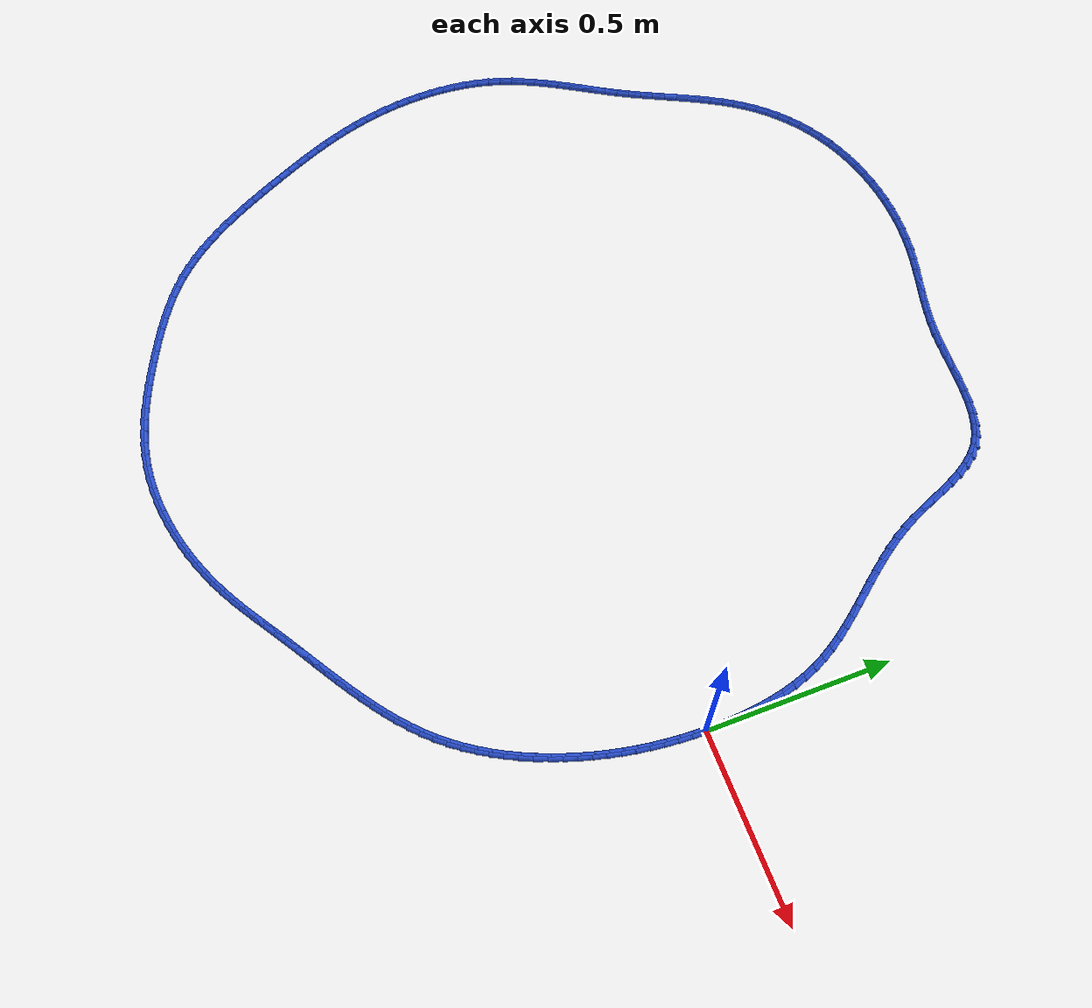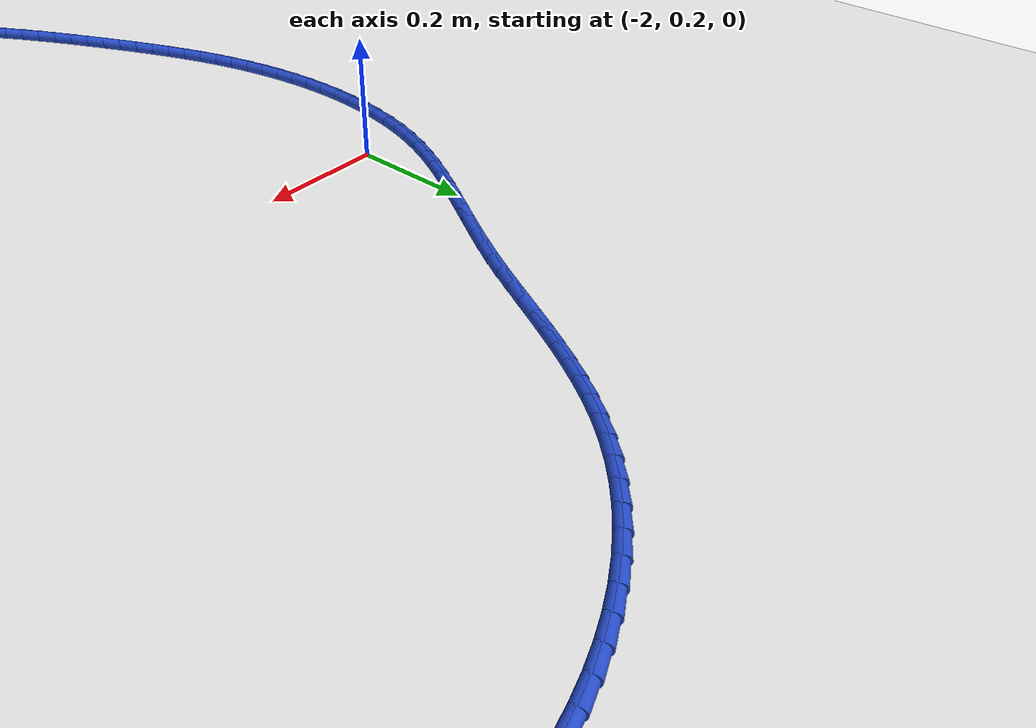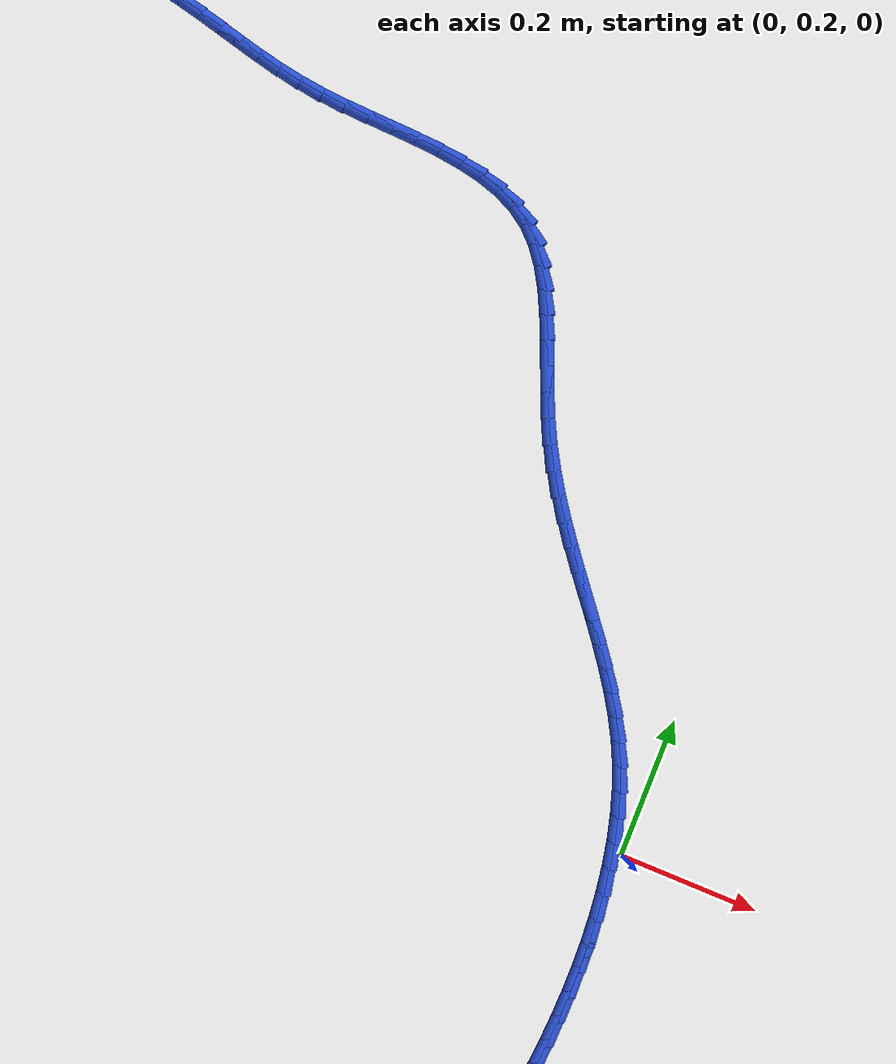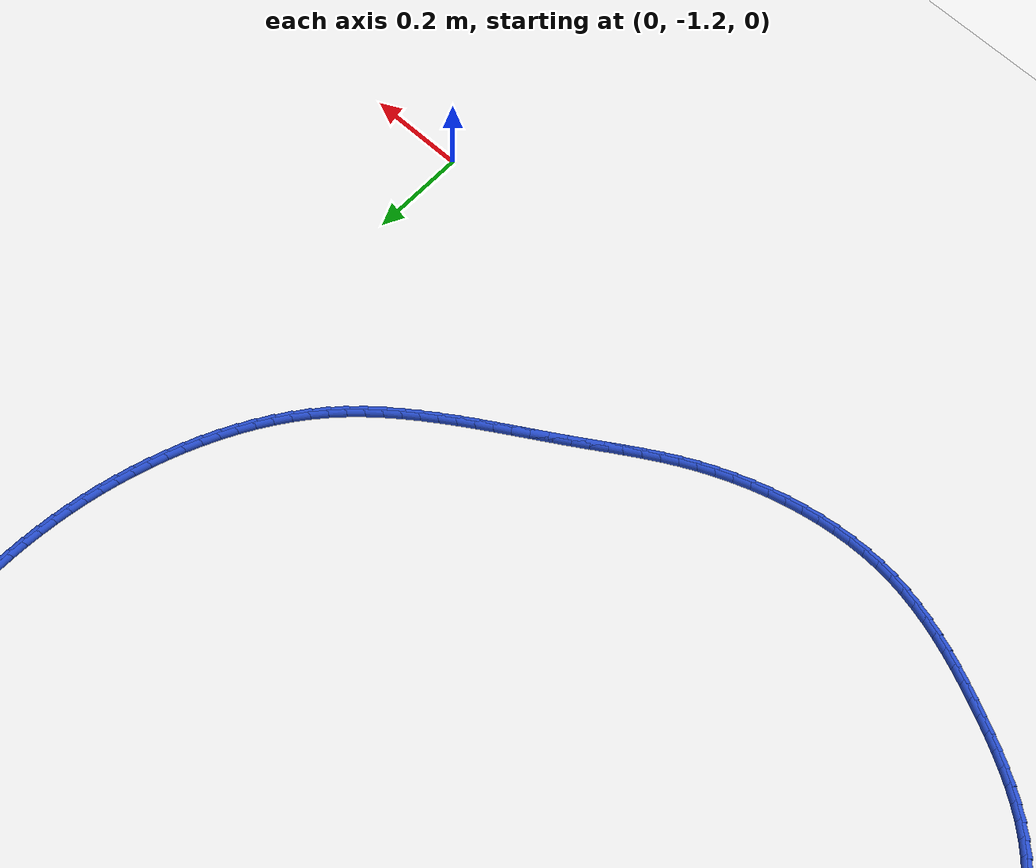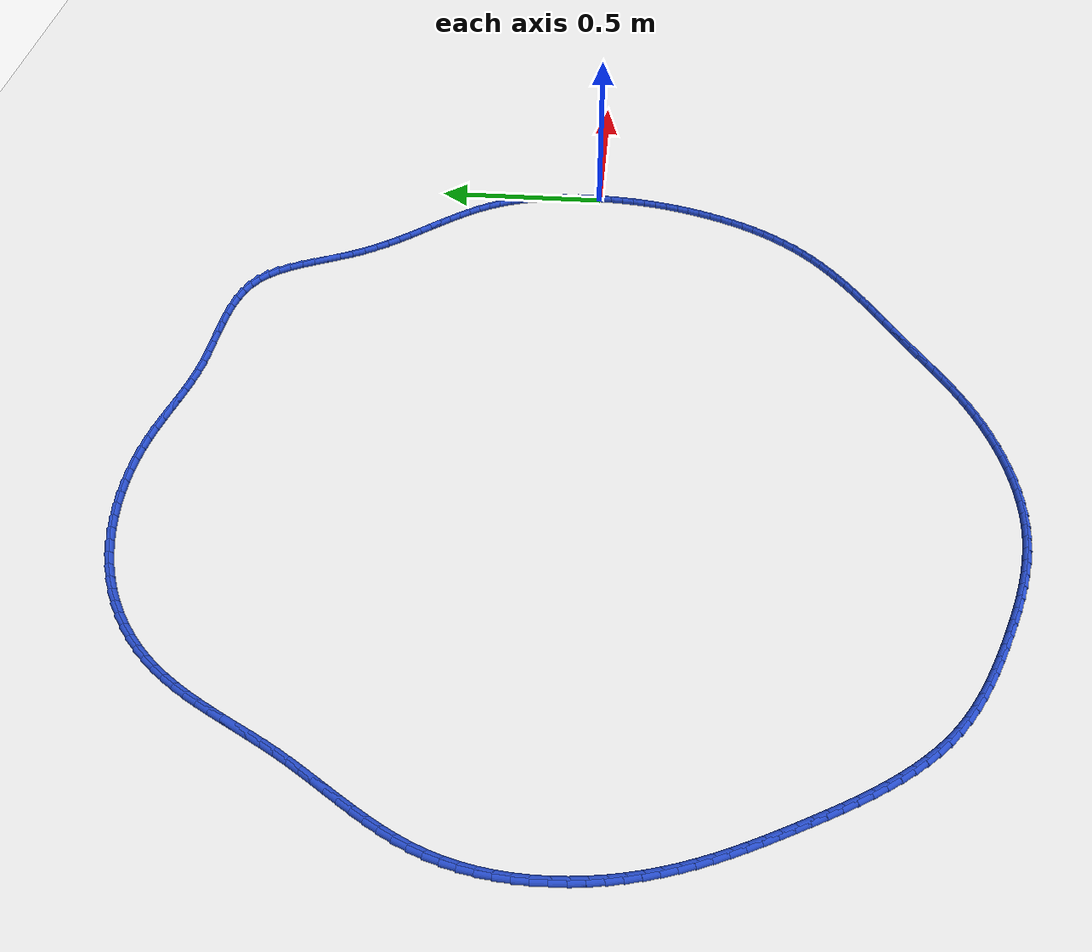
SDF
<sdf version="1.6">
 <world name="default">
  <light name="sun" type="directional">
   <pose>0 0 10 0 -0 0</pose>
   <diffuse>0.8 0.8 0.8 1</diffuse>
   <specular>0.2 0.2 0.2 1</specular>
   <attenuation>
    <range>1000</range>
    <constant>0.9</constant>
    <linear>0.01</linear>
    <quadratic>0.001</quadratic>
   </attenuation>
   <direction>-0.5 0.1 -0.9</direction>
  </light>
  <model name="ground_plane">
   <static>1</static>
   <link name="link">
    <collision name="collision">
     <geometry><plane><normal>0 0 1</normal><size>100 100</size></plane></geometry>
     <surface><friction><ode><mu>100</mu><mu2>50</mu2></ode></friction></surface>
    </collision>
    <visual name="visual">
     <cast_shadows>0</cast_shadows>
     <geometry><plane><normal>0 0 1</normal><size>100 100</size></plane></geometry>
     <material>
      <script><uri>file://media/materials/scripts/gazebo.material</uri><name>Gazebo/WhiteGlow</name></script>
     </material>
    </visual>
   </link>
  </model>
  <gravity>0 0 -9.8</gravity>
  <magnetic_field>6e-06 2.3e-05 -4.2e-05</magnetic_field>
  <atmosphere type="adiabatic"/>
  <physics name="default_physics" default="0" type="ode">
   <max_step_size>0.001</max_step_size>
   <real_time_factor>1</real_time_factor>
   <real_time_update_rate>1000</real_time_update_rate>
  </physics>
  <scene><ambient>0.4 0.4 0.4 1</ambient><background>0.7 0.7 0.7 1</background><shadows>1</shadows></scene>
  <spherical_coordinates>
   <surface_model>EARTH_WGS84</surface_model>
   <latitude_deg>0</latitude_deg>
   <longitude_deg>0</longitude_deg>
   <elevation>0</elevation>
   <heading_deg>0</heading_deg>
  </spherical_coordinates>
  <model name="line">
   <link name="link_0">
    <pose>1.214306433183765e-17 2.7755575615628914e-17 0.01 0 1.57 1.5646358276059467</pose>
    <collision name="collision">
     <geometry><cylinder><radius>0.01</radius><length>0.08</length></cylinder></geometry>
    </collision>
    <visual name="visual">
     <material>
      <script><name>Gazebo/Blue</name><uri>file://media/materials/scripts/gazebo.material</uri></script>
     </material>
     <geometry><cylinder><radius>0.01</radius><length>0.08</length></cylinder></geometry>
    </visual>
   </link>
   <link name="link_1">
    <pose>0.00022275718261299585 0.036158492642460245 0.01 0 1.57 -1.5446809342096588</pose>
    <collision name="collision">
     <geometry><cylinder><radius>0.01</radius><length>0.08</length></cylinder></geometry>
    </collision>
    <visual name="visual">
     <material>
      <script><name>Gazebo/Blue</name><uri>file://media/materials/scripts/gazebo.material</uri></script>
     </material>
     <geometry><cylinder><radius>0.01</radius><length>0.08</length></cylinder></geometry>
    </visual>
   </link>
   <link name="link_2">
    <pose>-0.0007243705754948649 0.07241727861252063 0.01 0 1.57 -1.5091059318863258</pose>
    <collision name="collision">
     <geometry><cylinder><radius>0.01</radius><length>0.08</length></cylinder></geometry>
    </collision>
    <visual name="visual">
     <material>
      <script><name>Gazebo/Blue</name><uri>file://media/materials/scripts/gazebo.material</uri></script>
     </material>
     <geometry><cylinder><radius>0.01</radius><length>0.08</length></cylinder></geometry>
    </visual>
   </link>
   <link name="link_3">
    <pose>-0.002960141446029911 0.10861309039161447 0.01 0 1.57 -1.469855717839882</pose>
    <collision name="collision">
     <geometry><cylinder><radius>0.01</radius><length>0.08</length></cylinder></geometry>
    </collision>
    <visual name="visual">
     <material>
      <script><name>Gazebo/Blue</name><uri>file://media/materials/scripts/gazebo.material</uri></script>
     </material>
     <geometry><cylinder><radius>0.01</radius><length>0.08</length></cylinder></geometry>
    </visual>
   </link>
   <link name="link_4">
    <pose>-0.006603313600698487 0.1445826604611752 0.01 0 1.57 -1.4265185151365294</pose>
    <collision name="collision">
     <geometry><cylinder><radius>0.01</radius><length>0.08</length></cylinder></geometry>
    </collision>
    <visual name="visual">
     <material>
      <script><name>Gazebo/Blue</name><uri>file://media/materials/scripts/gazebo.material</uri></script>
     </material>
     <geometry><cylinder><radius>0.01</radius><length>0.08</length></cylinder></geometry>
    </visual>
   </link>
   <link name="link_5">
    <pose>-0.011772645211206944 0.18016272130263614 0.01 0 1.57 -1.3786550982861463</pose>
    <collision name="collision">
     <geometry><cylinder><radius>0.01</radius><length>0.08</length></cylinder></geometry>
    </collision>
    <visual name="visual">
     <material>
      <script><name>Gazebo/Blue</name><uri>file://media/materials/scripts/gazebo.material</uri></script>
     </material>
     <geometry><cylinder><radius>0.01</radius><length>0.08</length></cylinder></geometry>
    </visual>
   </link>
   <link name="link_6">
    <pose>-0.01858689444926162 0.21519000539743074 0.01 0 1.57 -1.3258145069641336</pose>
    <collision name="collision">
     <geometry><cylinder><radius>0.01</radius><length>0.08</length></cylinder></geometry>
    </collision>
    <visual name="visual">
     <material>
      <script><name>Gazebo/Blue</name><uri>file://media/materials/scripts/gazebo.material</uri></script>
     </material>
     <geometry><cylinder><radius>0.01</radius><length>0.08</length></cylinder></geometry>
    </visual>
   </link>
   <link name="link_7">
    <pose>-0.02716481948656886 0.24950124522699213 0.01 0 1.57 -1.2675604716059123</pose>
    <collision name="collision">
     <geometry><cylinder><radius>0.01</radius><length>0.08</length></cylinder></geometry>
    </collision>
    <visual name="visual">
     <material>
      <script><name>Gazebo/Blue</name><uri>file://media/materials/scripts/gazebo.material</uri></script>
     </material>
     <geometry><cylinder><radius>0.01</radius><length>0.08</length></cylinder></geometry>
    </visual>
   </link>
   <link name="link_8">
    <pose>-0.037625178494835 0.28293317327275386 0.01 0 1.57 -1.203511974484743</pose>
    <collision name="collision">
     <geometry><cylinder><radius>0.01</radius><length>0.08</length></cylinder></geometry>
    </collision>
    <visual name="visual">
     <material>
      <script><name>Gazebo/Blue</name><uri>file://media/materials/scripts/gazebo.material</uri></script>
     </material>
     <geometry><cylinder><radius>0.01</radius><length>0.08</length></cylinder></geometry>
    </visual>
   </link>
   <link name="link_9">
    <pose>-0.0500867296457664 0.3153225220161492 0.01 0 1.57 -1.1343039813078486</pose>
    <collision name="collision">
     <geometry><cylinder><radius>0.01</radius><length>0.08</length></cylinder></geometry>
    </collision>
    <visual name="visual">
     <material>
      <script><name>Gazebo/Blue</name><uri>file://media/materials/scripts/gazebo.material</uri></script>
     </material>
     <geometry><cylinder><radius>0.01</radius><length>0.08</length></cylinder></geometry>
    </visual>
   </link>
   <link name="link_10">
    <pose>-0.06464413219384604 0.3465279334582203 0.01 0 1.57 -1.0693498294287862</pose>
    <collision name="collision">
     <geometry><cylinder><radius>0.01</radius><length>0.08</length></cylinder></geometry>
    </collision>
    <visual name="visual">
     <material>
      <script><name>Gazebo/Blue</name><uri>file://media/materials/scripts/gazebo.material</uri></script>
     </material>
     <geometry><cylinder><radius>0.01</radius><length>0.08</length></cylinder></geometry>
    </visual>
   </link>
   <link name="link_11">
    <pose>-0.08114633587859307 0.3766314362935382 0.01 0 1.57 -1.0148216413763047</pose>
    <collision name="collision">
     <geometry><cylinder><radius>0.01</radius><length>0.08</length></cylinder></geometry>
    </collision>
    <visual name="visual">
     <material>
      <script><name>Gazebo/Blue</name><uri>file://media/materials/scripts/gazebo.material</uri></script>
     </material>
     <geometry><cylinder><radius>0.01</radius><length>0.08</length></cylinder></geometry>
    </visual>
   </link>
   <link name="link_12">
    <pose>-0.0992987237941108 0.4058455827669126 0.01 0 1.57 -0.9712359862877464</pose>
    <collision name="collision">
     <geometry><cylinder><radius>0.01</radius><length>0.08</length></cylinder></geometry>
    </collision>
    <visual name="visual">
     <material>
      <script><name>Gazebo/Blue</name><uri>file://media/materials/scripts/gazebo.material</uri></script>
     </material>
     <geometry><cylinder><radius>0.01</radius><length>0.08</length></cylinder></geometry>
    </visual>
   </link>
   <link name="link_13">
    <pose>-0.11880487657426363 0.43438456382905805 0.01 0 1.57 -0.9386740257295672</pose>
    <collision name="collision">
     <geometry><cylinder><radius>0.01</radius><length>0.08</length></cylinder></geometry>
    </collision>
    <visual name="visual">
     <material>
      <script><name>Gazebo/Blue</name><uri>file://media/materials/scripts/gazebo.material</uri></script>
     </material>
     <geometry><cylinder><radius>0.01</radius><length>0.08</length></cylinder></geometry>
    </visual>
   </link>
   <link name="link_14">
    <pose>-0.13936837485291595 0.46246257043068856 0.01 0 1.57 -0.9170043819340471</pose>
    <collision name="collision">
     <geometry><cylinder><radius>0.01</radius><length>0.08</length></cylinder></geometry>
    </collision>
    <visual name="visual">
     <material>
      <script><name>Gazebo/Blue</name><uri>file://media/materials/scripts/gazebo.material</uri></script>
     </material>
     <geometry><cylinder><radius>0.01</radius><length>0.08</length></cylinder></geometry>
    </visual>
   </link>
   <link name="link_15">
    <pose>-0.16069279926393235 0.4902937935225187 0.01 0 1.57 -0.9060036631063859</pose>
    <collision name="collision">
     <geometry><cylinder><radius>0.01</radius><length>0.08</length></cylinder></geometry>
    </collision>
    <visual name="visual">
     <material>
      <script><name>Gazebo/Blue</name><uri>file://media/materials/scripts/gazebo.material</uri></script>
     </material>
     <geometry><cylinder><radius>0.01</radius><length>0.08</length></cylinder></geometry>
    </visual>
   </link>
   <link name="link_16">
    <pose>-0.1824817304411771 0.5180924240552627 0.01 0 1.57 -0.9054338920843115</pose>
    <collision name="collision">
     <geometry><cylinder><radius>0.01</radius><length>0.08</length></cylinder></geometry>
    </collision>
    <visual name="visual">
     <material>
      <script><name>Gazebo/Blue</name><uri>file://media/materials/scripts/gazebo.material</uri></script>
     </material>
     <geometry><cylinder><radius>0.01</radius><length>0.08</length></cylinder></geometry>
    </visual>
   </link>
   <link name="link_17">
    <pose>-0.20443874901851475 0.5460726529796347 0.01 0 1.57 -0.9150789978626155</pose>
    <collision name="collision">
     <geometry><cylinder><radius>0.01</radius><length>0.08</length></cylinder></geometry>
    </collision>
    <visual name="visual">
     <material>
      <script><name>Gazebo/Blue</name><uri>file://media/materials/scripts/gazebo.material</uri></script>
     </material>
     <geometry><cylinder><radius>0.01</radius><length>0.08</length></cylinder></geometry>
    </visual>
   </link>
   <link name="link_18">
    <pose>-0.22626743562980964 0.5744486712463492 0.01 0 1.57 -0.9347456010967117</pose>
    <collision name="collision">
     <geometry><cylinder><radius>0.01</radius><length>0.08</length></cylinder></geometry>
    </collision>
    <visual name="visual">
     <material>
      <script><name>Gazebo/Blue</name><uri>file://media/materials/scripts/gazebo.material</uri></script>
     </material>
     <geometry><cylinder><radius>0.01</radius><length>0.08</length></cylinder></geometry>
    </visual>
   </link>
   <link name="link_19">
    <pose>-0.2476713709089263 0.6034346698061206 0.01 0 1.57 -0.9642329522671258</pose>
    <collision name="collision">
     <geometry><cylinder><radius>0.01</radius><length>0.08</length></cylinder></geometry>
    </collision>
    <visual name="visual">
     <material>
      <script><name>Gazebo/Blue</name><uri>file://media/materials/scripts/gazebo.material</uri></script>
     </material>
     <geometry><cylinder><radius>0.01</radius><length>0.08</length></cylinder></geometry>
    </visual>
   </link>
   <link name="link_20">
    <pose>-0.26835413548972914 0.6332448396096632 0.01 0 1.57 -1.0032763263265234</pose>
    <collision name="collision">
     <geometry><cylinder><radius>0.01</radius><length>0.08</length></cylinder></geometry>
    </collision>
    <visual name="visual">
     <material>
      <script><name>Gazebo/Blue</name><uri>file://media/materials/scripts/gazebo.material</uri></script>
     </material>
     <geometry><cylinder><radius>0.01</radius><length>0.08</length></cylinder></geometry>
    </visual>
   </link>
   <link name="link_21">
    <pose>-0.2880193100060825 0.6640933716076909 0.01 0 1.57 -1.0514696932113152</pose>
    <collision name="collision">
     <geometry><cylinder><radius>0.01</radius><length>0.08</length></cylinder></geometry>
    </collision>
    <visual name="visual">
     <material>
      <script><name>Gazebo/Blue</name><uri>file://media/materials/scripts/gazebo.material</uri></script>
     </material>
     <geometry><cylinder><radius>0.01</radius><length>0.08</length></cylinder></geometry>
    </visual>
   </link>
   <link name="link_22">
    <pose>-0.306370475091851 0.6961944567509185 0.01 0 1.57 -1.1074434799144157</pose>
    <collision name="collision">
     <geometry><cylinder><radius>0.01</radius><length>0.08</length></cylinder></geometry>
    </collision>
    <visual name="visual">
     <material>
      <script><name>Gazebo/Blue</name><uri>file://media/materials/scripts/gazebo.material</uri></script>
     </material>
     <geometry><cylinder><radius>0.01</radius><length>0.08</length></cylinder></geometry>
    </visual>
   </link>
   <link name="link_23">
    <pose>-0.32313145726287845 0.7297411381782275 0.01 0 1.57 -1.15483543501018</pose>
    <collision name="collision">
     <geometry><cylinder><radius>0.01</radius><length>0.08</length></cylinder></geometry>
    </collision>
    <visual name="visual">
     <material>
      <script><name>Gazebo/Blue</name><uri>file://media/materials/scripts/gazebo.material</uri></script>
     </material>
     <geometry><cylinder><radius>0.01</radius><length>0.08</length></cylinder></geometry>
    </visual>
   </link>
   <link name="link_24">
    <pose>-0.3384695018997493 0.7644632863831213 0.01 0 1.57 -1.1794804909377974</pose>
    <collision name="collision">
     <geometry><cylinder><radius>0.01</radius><length>0.08</length></cylinder></geometry>
    </collision>
    <visual name="visual">
     <material>
      <script><name>Gazebo/Blue</name><uri>file://media/materials/scripts/gazebo.material</uri></script>
     </material>
     <geometry><cylinder><radius>0.01</radius><length>0.08</length></cylinder></geometry>
    </visual>
   </link>
   <link name="link_25">
    <pose>-0.352983260585647 0.7996401470256107 0.01 0 1.57 -1.181694854691323</pose>
    <collision name="collision">
     <geometry><cylinder><radius>0.01</radius><length>0.08</length></cylinder></geometry>
    </collision>
    <visual name="visual">
     <material>
      <script><name>Gazebo/Blue</name><uri>file://media/materials/scripts/gazebo.material</uri></script>
     </material>
     <geometry><cylinder><radius>0.01</radius><length>0.08</length></cylinder></geometry>
    </visual>
   </link>
   <link name="link_26">
    <pose>-0.3672892276851839 0.8345323281096836 0.01 0 1.57 -1.1609321161785238</pose>
    <collision name="collision">
     <geometry><cylinder><radius>0.01</radius><length>0.08</length></cylinder></geometry>
    </collision>
    <visual name="visual">
     <material>
      <script><name>Gazebo/Blue</name><uri>file://media/materials/scripts/gazebo.material</uri></script>
     </material>
     <geometry><cylinder><radius>0.01</radius><length>0.08</length></cylinder></geometry>
    </visual>
   </link>
   <link name="link_27">
    <pose>-0.3820038975629723 0.8684004376393286 0.01 0 1.57 -1.114964925242594</pose>
    <collision name="collision">
     <geometry><cylinder><radius>0.01</radius><length>0.08</length></cylinder></geometry>
    </collision>
    <visual name="visual">
     <material>
      <script><name>Gazebo/Blue</name><uri>file://media/materials/scripts/gazebo.material</uri></script>
     </material>
     <geometry><cylinder><radius>0.01</radius><length>0.08</length></cylinder></geometry>
    </visual>
   </link>
   <link name="link_28">
    <pose>-0.39774376458362404 0.9005050836185332 0.01 0 1.57 -1.0398571533578758</pose>
    <collision name="collision">
     <geometry><cylinder><radius>0.01</radius><length>0.08</length></cylinder></geometry>
    </collision>
    <visual name="visual">
     <material>
      <script><name>Gazebo/Blue</name><uri>file://media/materials/scripts/gazebo.material</uri></script>
     </material>
     <geometry><cylinder><radius>0.01</radius><length>0.08</length></cylinder></geometry>
    </visual>
   </link>
   <link name="link_29">
    <pose>-0.4151253231117518 0.9301068740512863 0.01 0 1.57 -0.9304569212374105</pose>
    <collision name="collision">
     <geometry><cylinder><radius>0.01</radius><length>0.08</length></cylinder></geometry>
    </collision>
    <visual name="visual">
     <material>
      <script><name>Gazebo/Blue</name><uri>file://media/materials/scripts/gazebo.material</uri></script>
     </material>
     <geometry><cylinder><radius>0.01</radius><length>0.08</length></cylinder></geometry>
    </visual>
   </link>
   <link name="link_30">
    <pose>-0.43476506751196714 0.9564664169415751 0.01 0 1.57 -0.7823570900033178</pose>
    <collision name="collision">
     <geometry><cylinder><radius>0.01</radius><length>0.08</length></cylinder></geometry>
    </collision>
    <visual name="visual">
     <material>
      <script><name>Gazebo/Blue</name><uri>file://media/materials/scripts/gazebo.material</uri></script>
     </material>
     <geometry><cylinder><radius>0.01</radius><length>0.08</length></cylinder></geometry>
    </visual>
   </link>
   <link name="link_31">
    <pose>-0.4572794921488828 0.978844320293388 0.01 0 1.57 -0.6028020230998821</pose>
    <collision name="collision">
     <geometry><cylinder><radius>0.01</radius><length>0.08</length></cylinder></geometry>
    </collision>
    <visual name="visual">
     <material>
      <script><name>Gazebo/Blue</name><uri>file://media/materials/scripts/gazebo.material</uri></script>
     </material>
     <geometry><cylinder><radius>0.01</radius><length>0.08</length></cylinder></geometry>
    </visual>
   </link>
   <link name="link_32">
    <pose>-0.48316314550023687 0.9966589572328235 0.01 0 1.57 -0.4373177974308187</pose>
    <collision name="collision">
     <geometry><cylinder><radius>0.01</radius><length>0.08</length></cylinder></geometry>
    </collision>
    <visual name="visual">
     <material>
      <script><name>Gazebo/Blue</name><uri>file://media/materials/scripts/gazebo.material</uri></script>
     </material>
     <geometry><cylinder><radius>0.01</radius><length>0.08</length></cylinder></geometry>
    </visual>
   </link>
   <link name="link_33">
    <pose>-0.5122079923193046 1.0102376549304726 0.01 0 1.57 -0.30500779651711574</pose>
    <collision name="collision">
     <geometry><cylinder><radius>0.01</radius><length>0.08</length></cylinder></geometry>
    </collision>
    <visual name="visual">
     <material>
      <script><name>Gazebo/Blue</name><uri>file://media/materials/scripts/gazebo.material</uri></script>
     </material>
     <geometry><cylinder><radius>0.01</radius><length>0.08</length></cylinder></geometry>
    </visual>
   </link>
   <link name="link_34">
    <pose>-0.5439549012439873 1.0202325912781687 0.01 0 1.57 -0.20490496469624225</pose>
    <collision name="collision">
     <geometry><cylinder><radius>0.01</radius><length>0.08</length></cylinder></geometry>
    </collision>
    <visual name="visual">
     <material>
      <script><name>Gazebo/Blue</name><uri>file://media/materials/scripts/gazebo.material</uri></script>
     </material>
     <geometry><cylinder><radius>0.01</radius><length>0.08</length></cylinder></geometry>
    </visual>
   </link>
   <link name="link_35">
    <pose>-0.5779444262157611 1.0272963513001305 0.01 0 1.57 -0.13297657358169426</pose>
    <collision name="collision">
     <geometry><cylinder><radius>0.01</radius><length>0.08</length></cylinder></geometry>
    </collision>
    <visual name="visual">
     <material>
      <script><name>Gazebo/Blue</name><uri>file://media/materials/scripts/gazebo.material</uri></script>
     </material>
     <geometry><cylinder><radius>0.01</radius><length>0.08</length></cylinder></geometry>
    </visual>
   </link>
   <link name="link_36">
    <pose>-0.6137171211761024 1.0320815200205775 0.01 0 1.57 -0.08495586529718346</pose>
    <collision name="collision">
     <geometry><cylinder><radius>0.01</radius><length>0.08</length></cylinder></geometry>
    </collision>
    <visual name="visual">
     <material>
      <script><name>Gazebo/Blue</name><uri>file://media/materials/scripts/gazebo.material</uri></script>
     </material>
     <geometry><cylinder><radius>0.01</radius><length>0.08</length></cylinder></geometry>
    </visual>
   </link>
   <link name="link_37">
    <pose>-0.6508135400664872 1.0352406824637286 0.01 0 1.57 -0.057515553515279275</pose>
    <collision name="collision">
     <geometry><cylinder><radius>0.01</radius><length>0.08</length></cylinder></geometry>
    </collision>
    <visual name="visual">
     <material>
      <script><name>Gazebo/Blue</name><uri>file://media/materials/scripts/gazebo.material</uri></script>
     </material>
     <geometry><cylinder><radius>0.01</radius><length>0.08</length></cylinder></geometry>
    </visual>
   </link>
   <link name="link_38">
    <pose>-0.6887742368283922 1.0374264236538036 0.01 0 1.57 -0.04857063870423929</pose>
    <collision name="collision">
     <geometry><cylinder><radius>0.01</radius><length>0.08</length></cylinder></geometry>
    </collision>
    <visual name="visual">
     <material>
      <script><name>Gazebo/Blue</name><uri>file://media/materials/scripts/gazebo.material</uri></script>
     </material>
     <geometry><cylinder><radius>0.01</radius><length>0.08</length></cylinder></geometry>
    </visual>
   </link>
   <link name="link_39">
    <pose>-0.7271397654032938 1.0392913286150214 0.01 0 1.57 -0.0572748340004048</pose>
    <collision name="collision">
     <geometry><cylinder><radius>0.01</radius><length>0.08</length></cylinder></geometry>
    </collision>
    <visual name="visual">
     <material>
      <script><name>Gazebo/Blue</name><uri>file://media/materials/scripts/gazebo.material</uri></script>
     </material>
     <geometry><cylinder><radius>0.01</radius><length>0.08</length></cylinder></geometry>
    </visual>
   </link>
   <link name="link_40">
    <pose>-0.7654506797326682 1.0414879823716015 0.01 0 1.57 -0.08396225511309346</pose>
    <collision name="collision">
     <geometry><cylinder><radius>0.01</radius><length>0.08</length></cylinder></geometry>
    </collision>
    <visual name="visual">
     <material>
      <script><name>Gazebo/Blue</name><uri>file://media/materials/scripts/gazebo.material</uri></script>
     </material>
     <geometry><cylinder><radius>0.01</radius><length>0.08</length></cylinder></geometry>
    </visual>
   </link>
   <link name="link_41">
    <pose>-0.8032475337579917 1.0446689699477634 0.01 0 1.57 -0.1295205380880872</pose>
    <collision name="collision">
     <geometry><cylinder><radius>0.01</radius><length>0.08</length></cylinder></geometry>
    </collision>
    <visual name="visual">
     <material>
      <script><name>Gazebo/Blue</name><uri>file://media/materials/scripts/gazebo.material</uri></script>
     </material>
     <geometry><cylinder><radius>0.01</radius><length>0.08</length></cylinder></geometry>
    </visual>
   </link>
   <link name="link_42">
    <pose>-0.8400833501035145 1.049466823664401 0.01 0 1.57 -0.18046137912852375</pose>
    <collision name="collision">
     <geometry><cylinder><radius>0.01</radius><length>0.08</length></cylinder></geometry>
    </collision>
    <visual name="visual">
     <material>
      <script><name>Gazebo/Blue</name><uri>file://media/materials/scripts/gazebo.material</uri></script>
     </material>
     <geometry><cylinder><radius>0.01</radius><length>0.08</length></cylinder></geometry>
    </visual>
   </link>
   <link name="link_43">
    <pose>-0.8758370497741585 1.055989951228765 0.01 0 1.57 -0.21975139844009897</pose>
    <collision name="collision">
     <geometry><cylinder><radius>0.01</radius><length>0.08</length></cylinder></geometry>
    </collision>
    <visual name="visual">
     <material>
      <script><name>Gazebo/Blue</name><uri>file://media/materials/scripts/gazebo.material</uri></script>
     </material>
     <geometry><cylinder><radius>0.01</radius><length>0.08</length></cylinder></geometry>
    </visual>
   </link>
   <link name="link_44">
    <pose>-0.9107367906990066 1.0637851016262407 0.01 0 1.57 -0.24535136960140017</pose>
    <collision name="collision">
     <geometry><cylinder><radius>0.01</radius><length>0.08</length></cylinder></geometry>
    </collision>
    <visual name="visual">
     <material>
      <script><name>Gazebo/Blue</name><uri>file://media/materials/scripts/gazebo.material</uri></script>
     </material>
     <geometry><cylinder><radius>0.01</radius><length>0.08</length></cylinder></geometry>
    </visual>
   </link>
   <link name="link_45">
    <pose>-0.9450278741995402 1.0723714530580353 0.01 0 1.57 -0.2564519328983843</pose>
    <collision name="collision">
     <geometry><cylinder><radius>0.01</radius><length>0.08</length></cylinder></geometry>
    </collision>
    <visual name="visual">
     <material>
      <script><name>Gazebo/Blue</name><uri>file://media/materials/scripts/gazebo.material</uri></script>
     </material>
     <geometry><cylinder><radius>0.01</radius><length>0.08</length></cylinder></geometry>
    </visual>
   </link>
   <link name="link_46">
    <pose>-0.9789556015972408 1.0812681837253542 0.01 0 1.57 -0.2525878655030559</pose>
    <collision name="collision">
     <geometry><cylinder><radius>0.01</radius><length>0.08</length></cylinder></geometry>
    </collision>
    <visual name="visual">
     <material>
      <script><name>Gazebo/Blue</name><uri>file://media/materials/scripts/gazebo.material</uri></script>
     </material>
     <geometry><cylinder><radius>0.01</radius><length>0.08</length></cylinder></geometry>
    </visual>
   </link>
   <link name="link_47">
    <pose>-1.0127652742135906 1.0899944718294032 0.01 0 1.57 -0.23359830717002084</pose>
    <collision name="collision">
     <geometry><cylinder><radius>0.01</radius><length>0.08</length></cylinder></geometry>
    </collision>
    <visual name="visual">
     <material>
      <script><name>Gazebo/Blue</name><uri>file://media/materials/scripts/gazebo.material</uri></script>
     </material>
     <geometry><cylinder><radius>0.01</radius><length>0.08</length></cylinder></geometry>
    </visual>
   </link>
   <link name="link_48">
    <pose>-1.046702193370071 1.0980694955713892 0.01 0 1.57 -0.19966582469570557</pose>
    <collision name="collision">
     <geometry><cylinder><radius>0.01</radius><length>0.08</length></cylinder></geometry>
    </collision>
    <visual name="visual">
     <material>
      <script><name>Gazebo/Blue</name><uri>file://media/materials/scripts/gazebo.material</uri></script>
     </material>
     <geometry><cylinder><radius>0.01</radius><length>0.08</length></cylinder></geometry>
    </visual>
   </link>
   <link name="link_49">
    <pose>-1.0810116603881643 1.1050124331525182 0.01 0 1.57 -0.15314128835917507</pose>
    <collision name="collision">
     <geometry><cylinder><radius>0.01</radius><length>0.08</length></cylinder></geometry>
    </collision>
    <visual name="visual">
     <material>
      <script><name>Gazebo/Blue</name><uri>file://media/materials/scripts/gazebo.material</uri></script>
     </material>
     <geometry><cylinder><radius>0.01</radius><length>0.08</length></cylinder></geometry>
    </visual>
   </link>
   <link name="link_50">
    <pose>-1.1158939126349856 1.110396501670565 0.01 0 1.57 -0.10411077980259328</pose>
    <collision name="collision">
     <geometry><cylinder><radius>0.01</radius><length>0.08</length></cylinder></geometry>
    </collision>
    <visual name="visual">
     <material>
      <script><name>Gazebo/Blue</name><uri>file://media/materials/scripts/gazebo.material</uri></script>
     </material>
     <geometry><cylinder><radius>0.01</radius><length>0.08</length></cylinder></geometry>
    </visual>
   </link>
   <link name="link_51">
    <pose>-1.151298236279338 1.1140958488903991 0.01 0 1.57 -0.05562782732073192</pose>
    <collision name="collision">
     <geometry><cylinder><radius>0.01</radius><length>0.08</length></cylinder></geometry>
    </collision>
    <visual name="visual">
     <material>
      <script><name>Gazebo/Blue</name><uri>file://media/materials/scripts/gazebo.material</uri></script>
     </material>
     <geometry><cylinder><radius>0.01</radius><length>0.08</length></cylinder></geometry>
    </visual>
   </link>
   <link name="link_52">
    <pose>-1.1870870752499487 1.116088760327235 0.01 0 1.57 -0.007349846946834233</pose>
    <collision name="collision">
     <geometry><cylinder><radius>0.01</radius><length>0.08</length></cylinder></geometry>
    </collision>
    <visual name="visual">
     <material>
      <script><name>Gazebo/Blue</name><uri>file://media/materials/scripts/gazebo.material</uri></script>
     </material>
     <geometry><cylinder><radius>0.01</radius><length>0.08</length></cylinder></geometry>
    </visual>
   </link>
   <link name="link_53">
    <pose>-1.2231227895957277 1.1163536220816128 0.01 0 1.57 0.04105601154536369</pose>
    <collision name="collision">
     <geometry><cylinder><radius>0.01</radius><length>0.08</length></cylinder></geometry>
    </collision>
    <visual name="visual">
     <material>
      <script><name>Gazebo/Blue</name><uri>file://media/materials/scripts/gazebo.material</uri></script>
     </material>
     <geometry><cylinder><radius>0.01</radius><length>0.08</length></cylinder></geometry>
    </visual>
   </link>
   <link name="link_54">
    <pose>-1.2592677393655891 1.1148688202540762 0.01 0 1.57 0.0899117116685172</pose>
    <collision name="collision">
     <geometry><cylinder><radius>0.01</radius><length>0.08</length></cylinder></geometry>
    </collision>
    <visual name="visual">
     <material>
      <script><name>Gazebo/Blue</name><uri>file://media/materials/scripts/gazebo.material</uri></script>
     </material>
     <geometry><cylinder><radius>0.01</radius><length>0.08</length></cylinder></geometry>
    </visual>
   </link>
   <link name="link_55">
    <pose>-1.2953842846084422 1.1116127409451657 0.01 0 1.57 0.1395297038459506</pose>
    <collision name="collision">
     <geometry><cylinder><radius>0.01</radius><length>0.08</length></cylinder></geometry>
    </collision>
    <visual name="visual">
     <material>
      <script><name>Gazebo/Blue</name><uri>file://media/materials/scripts/gazebo.material</uri></script>
     </material>
     <geometry><cylinder><radius>0.01</radius><length>0.08</length></cylinder></geometry>
    </visual>
   </link>
   <link name="link_56">
    <pose>-1.3313347853732 1.1065637702554234 0.01 0 1.57 0.1902133277188427</pose>
    <collision name="collision">
     <geometry><cylinder><radius>0.01</radius><length>0.08</length></cylinder></geometry>
    </collision>
    <visual name="visual">
     <material>
      <script><name>Gazebo/Blue</name><uri>file://media/materials/scripts/gazebo.material</uri></script>
     </material>
     <geometry><cylinder><radius>0.01</radius><length>0.08</length></cylinder></geometry>
    </visual>
   </link>
   <link name="link_57">
    <pose>-1.366981601708774 1.0997002942853915 0.01 0 1.57 0.2422559096853807</pose>
    <collision name="collision">
     <geometry><cylinder><radius>0.01</radius><length>0.08</length></cylinder></geometry>
    </collision>
    <visual name="visual">
     <material>
      <script><name>Gazebo/Blue</name><uri>file://media/materials/scripts/gazebo.material</uri></script>
     </material>
     <geometry><cylinder><radius>0.01</radius><length>0.08</length></cylinder></geometry>
    </visual>
   </link>
   <link name="link_58">
    <pose>-1.4021870936640757 1.0910006991356112 0.01 0 1.57 0.2959381945803989</pose>
    <collision name="collision">
     <geometry><cylinder><radius>0.01</radius><length>0.08</length></cylinder></geometry>
    </collision>
    <visual name="visual">
     <material>
      <script><name>Gazebo/Blue</name><uri>file://media/materials/scripts/gazebo.material</uri></script>
     </material>
     <geometry><cylinder><radius>0.01</radius><length>0.08</length></cylinder></geometry>
    </visual>
   </link>
   <link name="link_59">
    <pose>-1.4368136212880163 1.080443370906625 0.01 0 1.57 0.35152372943716154</pose>
    <collision name="collision">
     <geometry><cylinder><radius>0.01</radius><length>0.08</length></cylinder></geometry>
    </collision>
    <visual name="visual">
     <material>
      <script><name>Gazebo/Blue</name><uri>file://media/materials/scripts/gazebo.material</uri></script>
     </material>
     <geometry><cylinder><radius>0.01</radius><length>0.08</length></cylinder></geometry>
    </visual>
   </link>
   <link name="link_60">
    <pose>-1.4707235446295075 1.0680066956989742 0.01 0 1.57 0.40925183034037727</pose>
    <collision name="collision">
     <geometry><cylinder><radius>0.01</radius><length>0.08</length></cylinder></geometry>
    </collision>
    <visual name="visual">
     <material>
      <script><name>Gazebo/Blue</name><uri>file://media/materials/scripts/gazebo.material</uri></script>
     </material>
     <geometry><cylinder><radius>0.01</radius><length>0.08</length></cylinder></geometry>
    </visual>
   </link>
   <link name="link_61">
    <pose>-1.5037792237374616 1.0536690596132003 0.01 0 1.57 0.4693249846592563</pose>
    <collision name="collision">
     <geometry><cylinder><radius>0.01</radius><length>0.08</length></cylinder></geometry>
    </collision>
    <visual name="visual">
     <material>
      <script><name>Gazebo/Blue</name><uri>file://media/materials/scripts/gazebo.material</uri></script>
     </material>
     <geometry><cylinder><radius>0.01</radius><length>0.08</length></cylinder></geometry>
    </visual>
   </link>
   <link name="link_62">
    <pose>-1.535843037401736 1.037408954651982 0.01 0 1.57 0.531002575170071</pose>
    <collision name="collision">
     <geometry><cylinder><radius>0.01</radius><length>0.08</length></cylinder></geometry>
    </collision>
    <visual name="visual">
     <material>
      <script><name>Gazebo/Blue</name><uri>file://media/materials/scripts/gazebo.material</uri></script>
     </material>
     <geometry><cylinder><radius>0.01</radius><length>0.08</length></cylinder></geometry>
    </visual>
   </link>
   <link name="link_63">
    <pose>-1.5667833674852367 1.01923879523867 0.01 0 1.57 0.5923176162015378</pose>
    <collision name="collision">
     <geometry><cylinder><radius>0.01</radius><length>0.08</length></cylinder></geometry>
    </collision>
    <visual name="visual">
     <material>
      <script><name>Gazebo/Blue</name><uri>file://media/materials/scripts/gazebo.material</uri></script>
     </material>
     <geometry><cylinder><radius>0.01</radius><length>0.08</length></cylinder></geometry>
    </visual>
   </link>
   <link name="link_64">
    <pose>-1.5964831584346513 0.9992532866648166 0.01 0 1.57 0.653265392172711</pose>
    <collision name="collision">
     <geometry><cylinder><radius>0.01</radius><length>0.08</length></cylinder></geometry>
    </collision>
    <visual name="visual">
     <material>
      <script><name>Gazebo/Blue</name><uri>file://media/materials/scripts/gazebo.material</uri></script>
     </material>
     <geometry><cylinder><radius>0.01</radius><length>0.08</length></cylinder></geometry>
    </visual>
   </link>
   <link name="link_65">
    <pose>-1.6248275200148539 0.9775593700941555 0.01 0 1.57 0.7141873135426705</pose>
    <collision name="collision">
     <geometry><cylinder><radius>0.01</radius><length>0.08</length></cylinder></geometry>
    </collision>
    <visual name="visual">
     <material>
      <script><name>Gazebo/Blue</name><uri>file://media/materials/scripts/gazebo.material</uri></script>
     </material>
     <geometry><cylinder><radius>0.01</radius><length>0.08</length></cylinder></geometry>
    </visual>
   </link>
   <link name="link_66">
    <pose>-1.6517015619907223 0.9542639866904217 0.01 0 1.57 0.7754357213492754</pose>
    <collision name="collision">
     <geometry><cylinder><radius>0.01</radius><length>0.08</length></cylinder></geometry>
    </collision>
    <visual name="visual">
     <material>
      <script><name>Gazebo/Blue</name><uri>file://media/materials/scripts/gazebo.material</uri></script>
     </material>
     <geometry><cylinder><radius>0.01</radius><length>0.08</length></cylinder></geometry>
    </visual>
   </link>
   <link name="link_67">
    <pose>-1.676990394127131 0.929474077617347 0.01 0 1.57 0.8373694479484927</pose>
    <collision name="collision">
     <geometry><cylinder><radius>0.01</radius><length>0.08</length></cylinder></geometry>
    </collision>
    <visual name="visual">
     <material>
      <script><name>Gazebo/Blue</name><uri>file://media/materials/scripts/gazebo.material</uri></script>
     </material>
     <geometry><cylinder><radius>0.01</radius><length>0.08</length></cylinder></geometry>
    </visual>
   </link>
   <link name="link_68">
    <pose>-1.7005791395002339 0.9032965858034078 0.01 0 1.57 0.8986542798066801</pose>
    <collision name="collision">
     <geometry><cylinder><radius>0.01</radius><length>0.08</length></cylinder></geometry>
    </collision>
    <visual name="visual">
     <material>
      <script><name>Gazebo/Blue</name><uri>file://media/materials/scripts/gazebo.material</uri></script>
     </material>
     <geometry><cylinder><radius>0.01</radius><length>0.08</length></cylinder></geometry>
    </visual>
   </link>
   <link name="link_69">
    <pose>-1.722421609306521 0.8758475604999287 0.01 0 1.57 0.953599439414233</pose>
    <collision name="collision">
     <geometry><cylinder><radius>0.01</radius><length>0.08</length></cylinder></geometry>
    </collision>
    <visual name="visual">
     <material>
      <script><name>Gazebo/Blue</name><uri>file://media/materials/scripts/gazebo.material</uri></script>
     </material>
     <geometry><cylinder><radius>0.01</radius><length>0.08</length></cylinder></geometry>
    </visual>
   </link>
   <link name="link_70">
    <pose>-1.7427003036556907 0.8472733693752428 0.01 0 1.57 1.0006414780373705</pose>
    <collision name="collision">
     <geometry><cylinder><radius>0.01</radius><length>0.08</length></cylinder></geometry>
    </collision>
    <visual name="visual">
     <material>
      <script><name>Gazebo/Blue</name><uri>file://media/materials/scripts/gazebo.material</uri></script>
     </material>
     <geometry><cylinder><radius>0.01</radius><length>0.08</length></cylinder></geometry>
    </visual>
   </link>
   <link name="link_71">
    <pose>-1.7616452567336112 0.8177266819245741 0.01 0 1.57 1.039596213281504</pose>
    <collision name="collision">
     <geometry><cylinder><radius>0.01</radius><length>0.08</length></cylinder></geometry>
    </collision>
    <visual name="visual">
     <material>
      <script><name>Gazebo/Blue</name><uri>file://media/materials/scripts/gazebo.material</uri></script>
     </material>
     <geometry><cylinder><radius>0.01</radius><length>0.08</length></cylinder></geometry>
    </visual>
   </link>
   <link name="link_72">
    <pose>-1.7794865027261504 0.7873601676431483 0.01 0 1.57 1.0704538960768264</pose>
    <collision name="collision">
     <geometry><cylinder><radius>0.01</radius><length>0.08</length></cylinder></geometry>
    </collision>
    <visual name="visual">
     <material>
      <script><name>Gazebo/Blue</name><uri>file://media/materials/scripts/gazebo.material</uri></script>
     </material>
     <geometry><cylinder><radius>0.01</radius><length>0.08</length></cylinder></geometry>
    </visual>
   </link>
   <link name="link_73">
    <pose>-1.796454075819175 0.75632649602619 0.01 0 1.57 1.0933028915591734</pose>
    <collision name="collision">
     <geometry><cylinder><radius>0.01</radius><length>0.08</length></cylinder></geometry>
    </collision>
    <visual name="visual">
     <material>
      <script><name>Gazebo/Blue</name><uri>file://media/materials/scripts/gazebo.material</uri></script>
     </material>
     <geometry><cylinder><radius>0.01</radius><length>0.08</length></cylinder></geometry>
    </visual>
   </link>
   <link name="link_74">
    <pose>-1.8127780101985547 0.7247783365689244 0.01 0 1.57 1.1082689704217006</pose>
    <collision name="collision">
     <geometry><cylinder><radius>0.01</radius><length>0.08</length></cylinder></geometry>
    </collision>
    <visual name="visual">
     <material>
      <script><name>Gazebo/Blue</name><uri>file://media/materials/scripts/gazebo.material</uri></script>
     </material>
     <geometry><cylinder><radius>0.01</radius><length>0.08</length></cylinder></geometry>
    </visual>
   </link>
   <link name="link_75">
    <pose>-1.8286883400501555 0.6928683587665766 0.01 0 1.57 1.1154722612779813</pose>
    <collision name="collision">
     <geometry><cylinder><radius>0.01</radius><length>0.08</length></cylinder></geometry>
    </collision>
    <visual name="visual">
     <material>
      <script><name>Gazebo/Blue</name><uri>file://media/materials/scripts/gazebo.material</uri></script>
     </material>
     <geometry><cylinder><radius>0.01</radius><length>0.08</length></cylinder></geometry>
    </visual>
   </link>
   <link name="link_76">
    <pose>-1.8444150995598463 0.6607492321143716 0.01 0 1.57 1.1150008338954642</pose>
    <collision name="collision">
     <geometry><cylinder><radius>0.01</radius><length>0.08</length></cylinder></geometry>
    </collision>
    <visual name="visual">
     <material>
      <script><name>Gazebo/Blue</name><uri>file://media/materials/scripts/gazebo.material</uri></script>
     </material>
     <geometry><cylinder><radius>0.01</radius><length>0.08</length></cylinder></geometry>
    </visual>
   </link>
   <link name="link_77">
    <pose>-1.8601883229134952 0.6285736261075346 0.01 0 1.57 1.1068990324487025</pose>
    <collision name="collision">
     <geometry><cylinder><radius>0.01</radius><length>0.08</length></cylinder></geometry>
    </collision>
    <visual name="visual">
     <material>
      <script><name>Gazebo/Blue</name><uri>file://media/materials/scripts/gazebo.material</uri></script>
     </material>
     <geometry><cylinder><radius>0.01</radius><length>0.08</length></cylinder></geometry>
    </visual>
   </link>
   <link name="link_78">
    <pose>-1.8762380442969695 0.5964942102412901 0.01 0 1.57 1.091169112447207</pose>
    <collision name="collision">
     <geometry><cylinder><radius>0.01</radius><length>0.08</length></cylinder></geometry>
    </collision>
    <visual name="visual">
     <material>
      <script><name>Gazebo/Blue</name><uri>file://media/materials/scripts/gazebo.material</uri></script>
     </material>
     <geometry><cylinder><radius>0.01</radius><length>0.08</length></cylinder></geometry>
    </visual>
   </link>
   <link name="link_79">
    <pose>-1.8927942978961378 0.5646636540108642 0.01 0 1.57 1.0683479902662012</pose>
    <collision name="collision">
     <geometry><cylinder><radius>0.01</radius><length>0.08</length></cylinder></geometry>
    </collision>
    <visual name="visual">
     <material>
      <script><name>Gazebo/Blue</name><uri>file://media/materials/scripts/gazebo.material</uri></script>
     </material>
     <geometry><cylinder><radius>0.01</radius><length>0.08</length></cylinder></geometry>
    </visual>
   </link>
   <link name="link_80">
    <pose>-1.9100694375321152 0.5332249161558642 0.01 0 1.57 1.0468837242007711</pose>
    <collision name="collision">
     <geometry><cylinder><radius>0.01</radius><length>0.08</length></cylinder></geometry>
    </collision>
    <visual name="visual">
     <material>
      <script><name>Gazebo/Blue</name><uri>file://media/materials/scripts/gazebo.material</uri></script>
     </material>
     <geometry><cylinder><radius>0.01</radius><length>0.08</length></cylinder></geometry>
    </visual>
   </link>
   <link name="link_81">
    <pose>-1.9280093425325109 0.5021745970844498 0.01 0 1.57 1.0333127197407073</pose>
    <collision name="collision">
     <geometry><cylinder><radius>0.01</radius><length>0.08</length></cylinder></geometry>
    </collision>
    <visual name="visual">
     <material>
      <script><name>Gazebo/Blue</name><uri>file://media/materials/scripts/gazebo.material</uri></script>
     </material>
     <geometry><cylinder><radius>0.01</radius><length>0.08</length></cylinder></geometry>
    </visual>
   </link>
   <link name="link_82">
    <pose>-1.946353771208603 0.47139608739009886 0.01 0 1.57 1.027797524962692</pose>
    <collision name="collision">
     <geometry><cylinder><radius>0.01</radius><length>0.08</length></cylinder></geometry>
    </collision>
    <visual name="visual">
     <material>
      <script><name>Gazebo/Blue</name><uri>file://media/materials/scripts/gazebo.material</uri></script>
     </material>
     <geometry><cylinder><radius>0.01</radius><length>0.08</length></cylinder></geometry>
    </visual>
   </link>
   <link name="link_83">
    <pose>-1.9648371223148928 0.44076983398572844 0.01 0 1.57 1.030363795955081</pose>
    <collision name="collision">
     <geometry><cylinder><radius>0.01</radius><length>0.08</length></cylinder></geometry>
    </collision>
    <visual name="visual">
     <material>
      <script><name>Gazebo/Blue</name><uri>file://media/materials/scripts/gazebo.material</uri></script>
     </material>
     <geometry><cylinder><radius>0.01</radius><length>0.08</length></cylinder></geometry>
    </visual>
   </link>
   <link name="link_84">
    <pose>-1.9831937946058846 0.4101762837842545 0.01 0 1.57 1.0410821133472825</pose>
    <collision name="collision">
     <geometry><cylinder><radius>0.01</radius><length>0.08</length></cylinder></geometry>
    </collision>
    <visual name="visual">
     <material>
      <script><name>Gazebo/Blue</name><uri>file://media/materials/scripts/gazebo.material</uri></script>
     </material>
     <geometry><cylinder><radius>0.01</radius><length>0.08</length></cylinder></geometry>
    </visual>
   </link>
   <link name="link_85">
    <pose>-2.001158186836081 0.37949588369859394 0.01 0 1.57 1.0600640031474318</pose>
    <collision name="collision">
     <geometry><cylinder><radius>0.01</radius><length>0.08</length></cylinder></geometry>
    </collision>
    <visual name="visual">
     <material>
      <script><name>Gazebo/Blue</name><uri>file://media/materials/scripts/gazebo.material</uri></script>
     </material>
     <geometry><cylinder><radius>0.01</radius><length>0.08</length></cylinder></geometry>
    </visual>
   </link>
   <link name="link_86">
    <pose>-2.0184646977599856 0.34860908064166385 0.01 0 1.57 1.0874415083119322</pose>
    <collision name="collision">
     <geometry><cylinder><radius>0.01</radius><length>0.08</length></cylinder></geometry>
    </collision>
    <visual name="visual">
     <material>
      <script><name>Gazebo/Blue</name><uri>file://media/materials/scripts/gazebo.material</uri></script>
     </material>
     <geometry><cylinder><radius>0.01</radius><length>0.08</length></cylinder></geometry>
    </visual>
   </link>
   <link name="link_87">
    <pose>-2.034847726132102 0.3173963215263802 0.01 0 1.57 1.12332831876361</pose>
    <collision name="collision">
     <geometry><cylinder><radius>0.01</radius><length>0.08</length></cylinder></geometry>
    </collision>
    <visual name="visual">
     <material>
      <script><name>Gazebo/Blue</name><uri>file://media/materials/scripts/gazebo.material</uri></script>
     </material>
     <geometry><cylinder><radius>0.01</radius><length>0.08</length></cylinder></geometry>
    </visual>
   </link>
   <link name="link_88">
    <pose>-2.0500416707069316 0.2857380532656597 0.01 0 1.57 1.1677606472636122</pose>
    <collision name="collision">
     <geometry><cylinder><radius>0.01</radius><length>0.08</length></cylinder></geometry>
    </collision>
    <visual name="visual">
     <material>
      <script><name>Gazebo/Blue</name><uri>file://media/materials/scripts/gazebo.material</uri></script>
     </material>
     <geometry><cylinder><radius>0.01</radius><length>0.08</length></cylinder></geometry>
    </visual>
   </link>
   <link name="link_89">
    <pose>-2.0637809302389796 0.2535147227724192 0.01 0 1.57 1.220618413463724</pose>
    <collision name="collision">
     <geometry><cylinder><radius>0.01</radius><length>0.08</length></cylinder></geometry>
    </collision>
    <visual name="visual">
     <material>
      <script><name>Gazebo/Blue</name><uri>file://media/materials/scripts/gazebo.material</uri></script>
     </material>
     <geometry><cylinder><radius>0.01</radius><length>0.08</length></cylinder></geometry>
    </visual>
   </link>
   <link name="link_90">
    <pose>-2.075799903482748 0.2206067769595757 0.01 0 1.57 1.2797369807946914</pose>
    <collision name="collision">
     <geometry><cylinder><radius>0.01</radius><length>0.08</length></cylinder></geometry>
    </collision>
    <visual name="visual">
     <material>
      <script><name>Gazebo/Blue</name><uri>file://media/materials/scripts/gazebo.material</uri></script>
     </material>
     <geometry><cylinder><radius>0.01</radius><length>0.08</length></cylinder></geometry>
    </visual>
   </link>
   <link name="link_91">
    <pose>-2.085887430314045 0.18693306636379878 0.01 0 1.57 1.3375905467505356</pose>
    <collision name="collision">
     <geometry><cylinder><radius>0.01</radius><length>0.08</length></cylinder></geometry>
    </collision>
    <visual name="visual">
     <material>
      <script><name>Gazebo/Blue</name><uri>file://media/materials/scripts/gazebo.material</uri></script>
     </material>
     <geometry><cylinder><radius>0.01</radius><length>0.08</length></cylinder></geometry>
    </visual>
   </link>
   <link name="link_92">
    <pose>-2.094050477713922 0.15256631181464986 0.01 0 1.57 1.3924423416790535</pose>
    <collision name="collision">
     <geometry><cylinder><radius>0.01</radius><length>0.08</length></cylinder></geometry>
    </collision>
    <visual name="visual">
     <material>
      <script><name>Gazebo/Blue</name><uri>file://media/materials/scripts/gazebo.material</uri></script>
     </material>
     <geometry><cylinder><radius>0.01</radius><length>0.08</length></cylinder></geometry>
    </visual>
   </link>
   <link name="link_93">
    <pose>-2.10035063524566 0.11761776577083377 0.01 0 1.57 1.4444549889144385</pose>
    <collision name="collision">
     <geometry><cylinder><radius>0.01</radius><length>0.08</length></cylinder></geometry>
    </collision>
    <visual name="visual">
     <material>
      <script><name>Gazebo/Blue</name><uri>file://media/materials/scripts/gazebo.material</uri></script>
     </material>
     <geometry><cylinder><radius>0.01</radius><length>0.08</length></cylinder></geometry>
    </visual>
   </link>
   <link name="link_94">
    <pose>-2.1048494924725465 0.08219868069106086 0.01 0 1.57 1.493830939239148</pose>
    <collision name="collision">
     <geometry><cylinder><radius>0.01</radius><length>0.08</length></cylinder></geometry>
    </collision>
    <visual name="visual">
     <material>
      <script><name>Gazebo/Blue</name><uri>file://media/materials/scripts/gazebo.material</uri></script>
     </material>
     <geometry><cylinder><radius>0.01</radius><length>0.08</length></cylinder></geometry>
    </visual>
   </link>
   <link name="link_95">
    <pose>-2.1076086389578683 0.04642030903404255 0.01 0 1.57 1.540798856566385</pose>
    <collision name="collision">
     <geometry><cylinder><radius>0.01</radius><length>0.08</length></cylinder></geometry>
    </collision>
    <visual name="visual">
     <material>
      <script><name>Gazebo/Blue</name><uri>file://media/materials/scripts/gazebo.material</uri></script>
     </material>
     <geometry><cylinder><radius>0.01</radius><length>0.08</length></cylinder></geometry>
    </visual>
   </link>
   <link name="link_96">
    <pose>-2.1086896642649138 0.010393903258489863 0.01 0 1.57 -1.5559893584545303</pose>
    <collision name="collision">
     <geometry><cylinder><radius>0.01</radius><length>0.08</length></cylinder></geometry>
    </collision>
    <visual name="visual">
     <material>
      <script><name>Gazebo/Blue</name><uri>file://media/materials/scripts/gazebo.material</uri></script>
     </material>
     <geometry><cylinder><radius>0.01</radius><length>0.08</length></cylinder></geometry>
    </visual>
   </link>
   <link name="link_97">
    <pose>-2.108154157956972 -0.025769284176886068 0.01 0 1.57 -1.513095251730046</pose>
    <collision name="collision">
     <geometry><cylinder><radius>0.01</radius><length>0.08</length></cylinder></geometry>
    </collision>
    <visual name="visual">
     <material>
      <script><name>Gazebo/Blue</name><uri>file://media/materials/scripts/gazebo.material</uri></script>
     </material>
     <geometry><cylinder><radius>0.01</radius><length>0.08</length></cylinder></geometry>
    </visual>
   </link>
   <link name="link_98">
    <pose>-2.1060637095973296 -0.06195800081337346 0.01 0 1.57 -1.471854429295454</pose>
    <collision name="collision">
     <geometry><cylinder><radius>0.01</radius><length>0.08</length></cylinder></geometry>
    </collision>
    <visual name="visual">
     <material>
      <script><name>Gazebo/Blue</name><uri>file://media/materials/scripts/gazebo.material</uri></script>
     </material>
     <geometry><cylinder><radius>0.01</radius><length>0.08</length></cylinder></geometry>
    </visual>
   </link>
   <link name="link_99">
    <pose>-2.1024799087492756 -0.0980609941922628 0.01 0 1.57 -1.4320084774964594</pose>
    <collision name="collision">
     <geometry><cylinder><radius>0.01</radius><length>0.08</length></cylinder></geometry>
    </collision>
    <visual name="visual">
     <material>
      <script><name>Gazebo/Blue</name><uri>file://media/materials/scripts/gazebo.material</uri></script>
     </material>
     <geometry><cylinder><radius>0.01</radius><length>0.08</length></cylinder></geometry>
    </visual>
   </link>
   <link name="link_100">
    <pose>-2.097464344976098 -0.13396701185484225 0.01 0 1.57 -1.3932983987134107</pose>
    <collision name="collision">
     <geometry><cylinder><radius>0.01</radius><length>0.08</length></cylinder></geometry>
    </collision>
    <visual name="visual">
     <material>
      <script><name>Gazebo/Blue</name><uri>file://media/materials/scripts/gazebo.material</uri></script>
     </material>
     <geometry><cylinder><radius>0.01</radius><length>0.08</length></cylinder></geometry>
    </visual>
   </link>
   <link name="link_101">
    <pose>-2.0910786078410837 -0.1695648013424007 0.01 0 1.57 -1.3554639687054484</pose>
    <collision name="collision">
     <geometry><cylinder><radius>0.01</radius><length>0.08</length></cylinder></geometry>
    </collision>
    <visual name="visual">
     <material>
      <script><name>Gazebo/Blue</name><uri>file://media/materials/scripts/gazebo.material</uri></script>
     </material>
     <geometry><cylinder><radius>0.01</radius><length>0.08</length></cylinder></geometry>
    </visual>
   </link>
   <link name="link_102">
    <pose>-2.0833842869075223 -0.20474311019622715 0.01 0 1.57 -1.3182588748457211</pose>
    <collision name="collision">
     <geometry><cylinder><radius>0.01</radius><length>0.08</length></cylinder></geometry>
    </collision>
    <visual name="visual">
     <material>
      <script><name>Gazebo/Blue</name><uri>file://media/materials/scripts/gazebo.material</uri></script>
     </material>
     <geometry><cylinder><radius>0.01</radius><length>0.08</length></cylinder></geometry>
    </visual>
   </link>
   <link name="link_103">
    <pose>-2.074443264861727 -0.23939197988669683 0.01 0 1.57 -1.282421338398297</pose>
    <collision name="collision">
     <geometry><cylinder><radius>0.01</radius><length>0.08</length></cylinder></geometry>
    </collision>
    <visual name="visual">
     <material>
      <script><name>Gazebo/Blue</name><uri>file://media/materials/scripts/gazebo.material</uri></script>
     </material>
     <geometry><cylinder><radius>0.01</radius><length>0.08</length></cylinder></geometry>
    </visual>
   </link>
   <link name="link_104">
    <pose>-2.064333504805873 -0.27347243545058886 0.01 0 1.57 -1.2494934949625074</pose>
    <collision name="collision">
     <geometry><cylinder><radius>0.01</radius><length>0.08</length></cylinder></geometry>
    </collision>
    <visual name="visual">
     <material>
      <script><name>Gazebo/Blue</name><uri>file://media/materials/scripts/gazebo.material</uri></script>
     </material>
     <geometry><cylinder><radius>0.01</radius><length>0.08</length></cylinder></geometry>
    </visual>
   </link>
   <link name="link_105">
    <pose>-2.0531570645627077 -0.30705186293004955 0.01 0 1.57 -1.219818836179564</pose>
    <collision name="collision">
     <geometry><cylinder><radius>0.01</radius><length>0.08</length></cylinder></geometry>
    </collision>
    <visual name="visual">
     <material>
      <script><name>Gazebo/Blue</name><uri>file://media/materials/scripts/gazebo.material</uri></script>
     </material>
     <geometry><cylinder><radius>0.01</radius><length>0.08</length></cylinder></geometry>
    </visual>
   </link>
   <link name="link_106">
    <pose>-2.0410179805657016 -0.3402063825222918 0.01 0 1.57 -1.1935685084286967</pose>
    <collision name="collision">
     <geometry><cylinder><radius>0.01</radius><length>0.08</length></cylinder></geometry>
    </collision>
    <visual name="visual">
     <material>
      <script><name>Gazebo/Blue</name><uri>file://media/materials/scripts/gazebo.material</uri></script>
     </material>
     <geometry><cylinder><radius>0.01</radius><length>0.08</length></cylinder></geometry>
    </visual>
   </link>
   <link name="link_107">
    <pose>-2.0280202892483246 -0.37301211442452675 0.01 0 1.57 -1.1708614371023203</pose>
    <collision name="collision">
     <geometry><cylinder><radius>0.01</radius><length>0.08</length></cylinder></geometry>
    </collision>
    <visual name="visual">
     <material>
      <script><name>Gazebo/Blue</name><uri>file://media/materials/scripts/gazebo.material</uri></script>
     </material>
     <geometry><cylinder><radius>0.01</radius><length>0.08</length></cylinder></geometry>
    </visual>
   </link>
   <link name="link_108">
    <pose>-2.014268027044046 -0.40554517883396596 0.01 0 1.57 -1.1517714535835317</pose>
    <collision name="collision">
     <geometry><cylinder><radius>0.01</radius><length>0.08</length></cylinder></geometry>
    </collision>
    <visual name="visual">
     <material>
      <script><name>Gazebo/Blue</name><uri>file://media/materials/scripts/gazebo.material</uri></script>
     </material>
     <geometry><cylinder><radius>0.01</radius><length>0.08</length></cylinder></geometry>
    </visual>
   </link>
   <link name="link_109">
    <pose>-1.9998652303863362 -0.437881695947821 0.01 0 1.57 -1.1363349049956704</pose>
    <collision name="collision">
     <geometry><cylinder><radius>0.01</radius><length>0.08</length></cylinder></geometry>
    </collision>
    <visual name="visual">
     <material>
      <script><name>Gazebo/Blue</name><uri>file://media/materials/scripts/gazebo.material</uri></script>
     </material>
     <geometry><cylinder><radius>0.01</radius><length>0.08</length></cylinder></geometry>
    </visual>
   </link>
   <link name="link_110">
    <pose>-1.9849159357086652 -0.47009778596330354 0.01 0 1.57 -1.1245579448075023</pose>
    <collision name="collision">
     <geometry><cylinder><radius>0.01</radius><length>0.08</length></cylinder></geometry>
    </collision>
    <visual name="visual">
     <material>
      <script><name>Gazebo/Blue</name><uri>file://media/materials/scripts/gazebo.material</uri></script>
     </material>
     <geometry><cylinder><radius>0.01</radius><length>0.08</length></cylinder></geometry>
    </visual>
   </link>
   <link name="link_111">
    <pose>-1.9695241794445029 -0.5022695690776252 0.01 0 1.57 -1.1163938345402686</pose>
    <collision name="collision">
     <geometry><cylinder><radius>0.01</radius><length>0.08</length></cylinder></geometry>
    </collision>
    <visual name="visual">
     <material>
      <script><name>Gazebo/Blue</name><uri>file://media/materials/scripts/gazebo.material</uri></script>
     </material>
     <geometry><cylinder><radius>0.01</radius><length>0.08</length></cylinder></geometry>
    </visual>
   </link>
   <link name="link_112">
    <pose>-1.9537932331109678 -0.5344723543067563 0.01 0 1.57 -1.1090708714474495</pose>
    <collision name="collision">
     <geometry><cylinder><radius>0.01</radius><length>0.08</length></cylinder></geometry>
    </collision>
    <visual name="visual">
     <material>
      <script><name>Gazebo/Blue</name><uri>file://media/materials/scripts/gazebo.material</uri></script>
     </material>
     <geometry><cylinder><radius>0.01</radius><length>0.08</length></cylinder></geometry>
    </visual>
   </link>
   <link name="link_113">
    <pose>-1.937754279989863 -0.56670500227598 0.01 0 1.57 -1.0976247592206017</pose>
    <collision name="collision">
     <geometry><cylinder><radius>0.01</radius><length>0.08</length></cylinder></geometry>
    </collision>
    <visual name="visual">
     <material>
      <script><name>Gazebo/Blue</name><uri>file://media/materials/scripts/gazebo.material</uri></script>
     </material>
     <geometry><cylinder><radius>0.01</radius><length>0.08</length></cylinder></geometry>
    </visual>
   </link>
   <link name="link_114">
    <pose>-1.9213083427480706 -0.5988283404141923 0.01 0 1.57 -1.0814899224492884</pose>
    <collision name="collision">
     <geometry><cylinder><radius>0.01</radius><length>0.08</length></cylinder></geometry>
    </collision>
    <visual name="visual">
     <material>
      <script><name>Gazebo/Blue</name><uri>file://media/materials/scripts/gazebo.material</uri></script>
     </material>
     <geometry><cylinder><radius>0.01</radius><length>0.08</length></cylinder></geometry>
    </visual>
   </link>
   <link name="link_115">
    <pose>-1.9043427776410118 -0.6306887031451827 0.01 0 1.57 -1.0605658219618876</pose>
    <collision name="collision">
     <geometry><cylinder><radius>0.01</radius><length>0.08</length></cylinder></geometry>
    </collision>
    <visual name="visual">
     <material>
      <script><name>Gazebo/Blue</name><uri>file://media/materials/scripts/gazebo.material</uri></script>
     </material>
     <geometry><cylinder><radius>0.01</radius><length>0.08</length></cylinder></geometry>
    </visual>
   </link>
   <link name="link_116">
    <pose>-1.8867449409241077 -0.6621324248927394 0.01 0 1.57 -1.0347058606775503</pose>
    <collision name="collision">
     <geometry><cylinder><radius>0.01</radius><length>0.08</length></cylinder></geometry>
    </collision>
    <visual name="visual">
     <material>
      <script><name>Gazebo/Blue</name><uri>file://media/materials/scripts/gazebo.material</uri></script>
     </material>
     <geometry><cylinder><radius>0.01</radius><length>0.08</length></cylinder></geometry>
    </visual>
   </link>
   <link name="link_117">
    <pose>-1.8684021888527804 -0.693005840080652 0.01 0 1.57 -1.0037295428385564</pose>
    <collision name="collision">
     <geometry><cylinder><radius>0.01</radius><length>0.08</length></cylinder></geometry>
    </collision>
    <visual name="visual">
     <material>
      <script><name>Gazebo/Blue</name><uri>file://media/materials/scripts/gazebo.material</uri></script>
     </material>
     <geometry><cylinder><radius>0.01</radius><length>0.08</length></cylinder></geometry>
    </visual>
   </link>
   <link name="link_118">
    <pose>-1.8492018776824526 -0.7231552831327092 0.01 0 1.57 -0.9674392342822672</pose>
    <collision name="collision">
     <geometry><cylinder><radius>0.01</radius><length>0.08</length></cylinder></geometry>
    </collision>
    <visual name="visual">
     <material>
      <script><name>Gazebo/Blue</name><uri>file://media/materials/scripts/gazebo.material</uri></script>
     </material>
     <geometry><cylinder><radius>0.01</radius><length>0.08</length></cylinder></geometry>
    </visual>
   </link>
   <link name="link_119">
    <pose>-1.8290313636685425 -0.7524270884727006 0.01 0 1.57 -0.9256432683921947</pose>
    <collision name="collision">
     <geometry><cylinder><radius>0.01</radius><length>0.08</length></cylinder></geometry>
    </collision>
    <visual name="visual">
     <material>
      <script><name>Gazebo/Blue</name><uri>file://media/materials/scripts/gazebo.material</uri></script>
     </material>
     <geometry><cylinder><radius>0.01</radius><length>0.08</length></cylinder></geometry>
    </visual>
   </link>
   <link name="link_120">
    <pose>-1.807778003066474 -0.7806675905244147 0.01 0 1.57 -0.8781869924907619</pose>
    <collision name="collision">
     <geometry><cylinder><radius>0.01</radius><length>0.08</length></cylinder></geometry>
    </collision>
    <visual name="visual">
     <material>
      <script><name>Gazebo/Blue</name><uri>file://media/materials/scripts/gazebo.material</uri></script>
     </material>
     <geometry><cylinder><radius>0.01</radius><length>0.08</length></cylinder></geometry>
    </visual>
   </link>
   <link name="link_121">
    <pose>-1.785329152131668 -0.8077231237116412 0.01 0 1.57 -0.8249925772867667</pose>
    <collision name="collision">
     <geometry><cylinder><radius>0.01</radius><length>0.08</length></cylinder></geometry>
    </collision>
    <visual name="visual">
     <material>
      <script><name>Gazebo/Blue</name><uri>file://media/materials/scripts/gazebo.material</uri></script>
     </material>
     <geometry><cylinder><radius>0.01</radius><length>0.08</length></cylinder></geometry>
    </visual>
   </link>
   <link name="link_122">
    <pose>-1.7615721671195455 -0.833440022458168 0.01 0 1.57 -0.7661066593591597</pose>
    <collision name="collision">
     <geometry><cylinder><radius>0.01</radius><length>0.08</length></cylinder></geometry>
    </collision>
    <visual name="visual">
     <material>
      <script><name>Gazebo/Blue</name><uri>file://media/materials/scripts/gazebo.material</uri></script>
     </material>
     <geometry><cylinder><radius>0.01</radius><length>0.08</length></cylinder></geometry>
    </visual>
   </link>
   <link name="link_123">
    <pose>-1.7363944042855284 -0.8576646211877849 0.01 0 1.57 -0.7036130317592312</pose>
    <collision name="collision">
     <geometry><cylinder><radius>0.01</radius><length>0.08</length></cylinder></geometry>
    </collision>
    <visual name="visual">
     <material>
      <script><name>Gazebo/Blue</name><uri>file://media/materials/scripts/gazebo.material</uri></script>
     </material>
     <geometry><cylinder><radius>0.01</radius><length>0.08</length></cylinder></geometry>
    </visual>
   </link>
   <link name="link_124">
    <pose>-1.7097274613022342 -0.8802910838188615 0.01 0 1.57 -0.6459238176580997</pose>
    <collision name="collision">
     <geometry><cylinder><radius>0.01</radius><length>0.08</length></cylinder></geometry>
    </collision>
    <visual name="visual">
     <material>
      <script><name>Gazebo/Blue</name><uri>file://media/materials/scripts/gazebo.material</uri></script>
     </material>
     <geometry><cylinder><radius>0.01</radius><length>0.08</length></cylinder></geometry>
    </visual>
   </link>
   <link name="link_125">
    <pose>-1.6816952857429563 -0.901421524175418 0.01 0 1.57 -0.5953635968045562</pose>
    <collision name="collision">
     <geometry><cylinder><radius>0.01</radius><length>0.08</length></cylinder></geometry>
    </collision>
    <visual name="visual">
     <material>
      <script><name>Gazebo/Blue</name><uri>file://media/materials/scripts/gazebo.material</uri></script>
     </material>
     <geometry><cylinder><radius>0.01</radius><length>0.08</length></cylinder></geometry>
    </visual>
   </link>
   <link name="link_126">
    <pose>-1.652474087280862 -0.9212145567539507 0.01 0 1.57 -0.5518635604594221</pose>
    <collision name="collision">
     <geometry><cylinder><radius>0.01</radius><length>0.08</length></cylinder></geometry>
    </collision>
    <visual name="visual">
     <material>
      <script><name>Gazebo/Blue</name><uri>file://media/materials/scripts/gazebo.material</uri></script>
     </material>
     <geometry><cylinder><radius>0.01</radius><length>0.08</length></cylinder></geometry>
    </visual>
   </link>
   <link name="link_127">
    <pose>-1.6222400766205975 -0.9398287971660867 0.01 0 1.57 -0.5152415955705227</pose>
    <collision name="collision">
     <geometry><cylinder><radius>0.01</radius><length>0.08</length></cylinder></geometry>
    </collision>
    <visual name="visual">
     <material>
      <script><name>Gazebo/Blue</name><uri>file://media/materials/scripts/gazebo.material</uri></script>
     </material>
     <geometry><cylinder><radius>0.01</radius><length>0.08</length></cylinder></geometry>
    </visual>
   </link>
   <link name="link_128">
    <pose>-1.591169464466809 -0.957422861023454 0.01 0 1.57 -0.48526670430023827</pose>
    <collision name="collision">
     <geometry><cylinder><radius>0.01</radius><length>0.08</length></cylinder></geometry>
    </collision>
    <visual name="visual">
     <material>
      <script><name>Gazebo/Blue</name><uri>file://media/materials/scripts/gazebo.material</uri></script>
     </material>
     <geometry><cylinder><radius>0.01</radius><length>0.08</length></cylinder></geometry>
    </visual>
   </link>
   <link name="link_129">
    <pose>-1.5594384615241441 -0.974155363937681 0.01 0 1.57 -0.4617079145705211</pose>
    <collision name="collision">
     <geometry><cylinder><radius>0.01</radius><length>0.08</length></cylinder></geometry>
    </collision>
    <visual name="visual">
     <material>
      <script><name>Gazebo/Blue</name><uri>file://media/materials/scripts/gazebo.material</uri></script>
     </material>
     <geometry><cylinder><radius>0.01</radius><length>0.08</length></cylinder></geometry>
    </visual>
   </link>
   <link name="link_130">
    <pose>-1.5272232784972473 -0.9901849215203946 0.01 0 1.57 -0.4442434927053829</pose>
    <collision name="collision">
     <geometry><cylinder><radius>0.01</radius><length>0.08</length></cylinder></geometry>
    </collision>
    <visual name="visual">
     <material>
      <script><name>Gazebo/Blue</name><uri>file://media/materials/scripts/gazebo.material</uri></script>
     </material>
     <geometry><cylinder><radius>0.01</radius><length>0.08</length></cylinder></geometry>
    </visual>
   </link>
   <link name="link_131">
    <pose>-1.494697912932977 -1.00566618017854 0.01 0 1.57 -0.42811389270785566</pose>
    <collision name="collision">
     <geometry><cylinder><radius>0.01</radius><length>0.08</length></cylinder></geometry>
    </collision>
    <visual name="visual">
     <material>
      <script><name>Gazebo/Blue</name><uri>file://media/materials/scripts/gazebo.material</uri></script>
     </material>
     <geometry><cylinder><radius>0.01</radius><length>0.08</length></cylinder></geometry>
    </visual>
   </link>
   <link name="link_132">
    <pose>-1.461955097993785 -1.0206080420902581 0.01 0 1.57 -0.4073662045899034</pose>
    <collision name="collision">
     <geometry><cylinder><radius>0.01</radius><length>0.08</length></cylinder></geometry>
    </collision>
    <visual name="visual">
     <material>
      <script><name>Gazebo/Blue</name><uri>file://media/materials/scripts/gazebo.material</uri></script>
     </material>
     <geometry><cylinder><radius>0.01</radius><length>0.08</length></cylinder></geometry>
    </visual>
   </link>
   <link name="link_133">
    <pose>-1.428984682186697 -1.0348348901652515 0.01 0 1.57 -0.3815037952314326</pose>
    <collision name="collision">
     <geometry><cylinder><radius>0.01</radius><length>0.08</length></cylinder></geometry>
    </collision>
    <visual name="visual">
     <material>
      <script><name>Gazebo/Blue</name><uri>file://media/materials/scripts/gazebo.material</uri></script>
     </material>
     <geometry><cylinder><radius>0.01</radius><length>0.08</length></cylinder></geometry>
    </visual>
   </link>
   <link name="link_134">
    <pose>-1.3957699012346958 -1.0481592475653416 0.01 0 1.57 -0.35038819204689503</pose>
    <collision name="collision">
     <geometry><cylinder><radius>0.01</radius><length>0.08</length></cylinder></geometry>
    </collision>
    <visual name="visual">
     <material>
      <script><name>Gazebo/Blue</name><uri>file://media/materials/scripts/gazebo.material</uri></script>
     </material>
     <geometry><cylinder><radius>0.01</radius><length>0.08</length></cylinder></geometry>
    </visual>
   </link>
   <link name="link_135">
    <pose>-1.3622939908607627 -1.0603936374523477 0.01 0 1.57 -0.31388241889313073</pose>
    <collision name="collision">
     <geometry><cylinder><radius>0.01</radius><length>0.08</length></cylinder></geometry>
    </collision>
    <visual name="visual">
     <material>
      <script><name>Gazebo/Blue</name><uri>file://media/materials/scripts/gazebo.material</uri></script>
     </material>
     <geometry><cylinder><radius>0.01</radius><length>0.08</length></cylinder></geometry>
    </visual>
   </link>
   <link name="link_136">
    <pose>-1.32854018678788 -1.0713505829880905 0.01 0 1.57 -0.27187687857296855</pose>
    <collision name="collision">
     <geometry><cylinder><radius>0.01</radius><length>0.08</length></cylinder></geometry>
    </collision>
    <visual name="visual">
     <material>
      <script><name>Gazebo/Blue</name><uri>file://media/materials/scripts/gazebo.material</uri></script>
     </material>
     <geometry><cylinder><radius>0.01</radius><length>0.08</length></cylinder></geometry>
    </visual>
   </link>
   <link name="link_137">
    <pose>-1.29449172473903 -1.080842607334391 0.01 0 1.57 -0.22432221070124067</pose>
    <collision name="collision">
     <geometry><cylinder><radius>0.01</radius><length>0.08</length></cylinder></geometry>
    </collision>
    <visual name="visual">
     <material>
      <script><name>Gazebo/Blue</name><uri>file://media/materials/scripts/gazebo.material</uri></script>
     </material>
     <geometry><cylinder><radius>0.01</radius><length>0.08</length></cylinder></geometry>
    </visual>
   </link>
   <link name="link_138">
    <pose>-1.260131840437195 -1.0886822336530702 0.01 0 1.57 -0.17126847700226103</pose>
    <collision name="collision">
     <geometry><cylinder><radius>0.01</radius><length>0.08</length></cylinder></geometry>
    </collision>
    <visual name="visual">
     <material>
      <script><name>Gazebo/Blue</name><uri>file://media/materials/scripts/gazebo.material</uri></script>
     </material>
     <geometry><cylinder><radius>0.01</radius><length>0.08</length></cylinder></geometry>
    </visual>
   </link>
   <link name="link_139">
    <pose>-1.2254437696053575 -1.0946819851059475 0.01 0 1.57 -0.11302842352202874</pose>
    <collision name="collision">
     <geometry><cylinder><radius>0.01</radius><length>0.08</length></cylinder></geometry>
    </collision>
    <visual name="visual">
     <material>
      <script><name>Gazebo/Blue</name><uri>file://media/materials/scripts/gazebo.material</uri></script>
     </material>
     <geometry><cylinder><radius>0.01</radius><length>0.08</length></cylinder></geometry>
    </visual>
   </link>
   <link name="link_140">
    <pose>-1.19041254664952 -1.0986584571568028 0.01 0 1.57 -0.05341590894806574</pose>
    <collision name="collision">
     <geometry><cylinder><radius>0.01</radius><length>0.08</length></cylinder></geometry>
    </collision>
    <visual name="visual">
     <material>
      <script><name>Gazebo/Blue</name><uri>file://media/materials/scripts/gazebo.material</uri></script>
     </material>
     <geometry><cylinder><radius>0.01</radius><length>0.08</length></cylinder></geometry>
    </visual>
   </link>
   <link name="link_141">
    <pose>-1.155076006377539 -1.1005477878332006 0.01 0 1.57 0.003536308424023887</pose>
    <collision name="collision">
     <geometry><cylinder><radius>0.01</radius><length>0.08</length></cylinder></geometry>
    </collision>
    <visual name="visual">
     <material>
      <script><name>Gazebo/Blue</name><uri>file://media/materials/scripts/gazebo.material</uri></script>
     </material>
     <geometry><cylinder><radius>0.01</radius><length>0.08</length></cylinder></geometry>
    </visual>
   </link>
   <link name="link_142">
    <pose>-1.1195320431991924 -1.100422092892831 0.01 0 1.57 0.05775378997066677</pose>
    <collision name="collision">
     <geometry><cylinder><radius>0.01</radius><length>0.08</length></cylinder></geometry>
    </collision>
    <visual name="visual">
     <material>
      <script><name>Gazebo/Blue</name><uri>file://media/materials/scripts/gazebo.material</uri></script>
     </material>
     <geometry><cylinder><radius>0.01</radius><length>0.08</length></cylinder></geometry>
    </visual>
   </link>
   <link name="link_143">
    <pose>-1.0838818096038574 -1.0983608645370222 0.01 0 1.57 0.10942598290560797</pose>
    <collision name="collision">
     <geometry><cylinder><radius>0.01</radius><length>0.08</length></cylinder></geometry>
    </collision>
    <visual name="visual">
     <material>
      <script><name>Gazebo/Blue</name><uri>file://media/materials/scripts/gazebo.material</uri></script>
     </material>
     <geometry><cylinder><radius>0.01</radius><length>0.08</length></cylinder></geometry>
    </visual>
   </link>
   <link name="link_144">
    <pose>-1.0482264580809113 -1.0944435949671025 0.01 0 1.57 0.15877393040625062</pose>
    <collision name="collision">
     <geometry><cylinder><radius>0.01</radius><length>0.08</length></cylinder></geometry>
    </collision>
    <visual name="visual">
     <material>
      <script><name>Gazebo/Blue</name><uri>file://media/materials/scripts/gazebo.material</uri></script>
     </material>
     <geometry><cylinder><radius>0.01</radius><length>0.08</length></cylinder></geometry>
    </visual>
   </link>
   <link name="link_145">
    <pose>-1.012667141119731 -1.0887497763844 0.01 0 1.57 0.20603939385537076</pose>
    <collision name="collision">
     <geometry><cylinder><radius>0.01</radius><length>0.08</length></cylinder></geometry>
    </collision>
    <visual name="visual">
     <material>
      <script><name>Gazebo/Blue</name><uri>file://media/materials/scripts/gazebo.material</uri></script>
     </material>
     <geometry><cylinder><radius>0.01</radius><length>0.08</length></cylinder></geometry>
    </visual>
   </link>
   <link name="link_146">
    <pose>-0.9773050112096926 -1.081358900990243 0.01 0 1.57 0.25147693855896297</pose>
    <collision name="collision">
     <geometry><cylinder><radius>0.01</radius><length>0.08</length></cylinder></geometry>
    </collision>
    <visual name="visual">
     <material>
      <script><name>Gazebo/Blue</name><uri>file://media/materials/scripts/gazebo.material</uri></script>
     </material>
     <geometry><cylinder><radius>0.01</radius><length>0.08</length></cylinder></geometry>
    </visual>
   </link>
   <link name="link_147">
    <pose>-0.9422412208401734 -1.072350460985959 0.01 0 1.57 0.2953486520144053</pose>
    <collision name="collision">
     <geometry><cylinder><radius>0.01</radius><length>0.08</length></cylinder></geometry>
    </collision>
    <visual name="visual">
     <material>
      <script><name>Gazebo/Blue</name><uri>file://media/materials/scripts/gazebo.material</uri></script>
     </material>
     <geometry><cylinder><radius>0.01</radius><length>0.08</length></cylinder></geometry>
    </visual>
   </link>
   <link name="link_148">
    <pose>-0.907576922500551 -1.0618039485728774 0.01 0 1.57 0.33792109111890517</pose>
    <collision name="collision">
     <geometry><cylinder><radius>0.01</radius><length>0.08</length></cylinder></geometry>
    </collision>
    <visual name="visual">
     <material>
      <script><name>Gazebo/Blue</name><uri>file://media/materials/scripts/gazebo.material</uri></script>
     </material>
     <geometry><cylinder><radius>0.01</radius><length>0.08</length></cylinder></geometry>
    </visual>
   </link>
   <link name="link_149">
    <pose>-0.8734132686802013 -1.0497988559523248 0.01 0 1.57 0.3794640661307618</pose>
    <collision name="collision">
     <geometry><cylinder><radius>0.01</radius><length>0.08</length></cylinder></geometry>
    </collision>
    <visual name="visual">
     <material>
      <script><name>Gazebo/Blue</name><uri>file://media/materials/scripts/gazebo.material</uri></script>
     </material>
     <geometry><cylinder><radius>0.01</radius><length>0.08</length></cylinder></geometry>
    </visual>
   </link>
   <link name="link_150">
    <pose>-0.8398514118685024 -1.036414675325631 0.01 0 1.57 0.4202509248569471</pose>
    <collision name="collision">
     <geometry><cylinder><radius>0.01</radius><length>0.08</length></cylinder></geometry>
    </collision>
    <visual name="visual">
     <material>
      <script><name>Gazebo/Blue</name><uri>file://media/materials/scripts/gazebo.material</uri></script>
     </material>
     <geometry><cylinder><radius>0.01</radius><length>0.08</length></cylinder></geometry>
    </visual>
   </link>
   <link name="link_151">
    <pose>-0.8069925045548302 -1.021730898894122 0.01 0 1.57 0.46056006619125656</pose>
    <collision name="collision">
     <geometry><cylinder><radius>0.01</radius><length>0.08</length></cylinder></geometry>
    </collision>
    <visual name="visual">
     <material>
      <script><name>Gazebo/Blue</name><uri>file://media/materials/scripts/gazebo.material</uri></script>
     </material>
     <geometry><cylinder><radius>0.01</radius><length>0.08</length></cylinder></geometry>
    </visual>
   </link>
   <link name="link_152">
    <pose>-0.7749376989265574 -1.0058270190121132 0.01 0 1.57 0.49922017986063255</pose>
    <collision name="collision">
     <geometry><cylinder><radius>0.01</radius><length>0.08</length></cylinder></geometry>
    </collision>
    <visual name="visual">
     <material>
      <script><name>Gazebo/Blue</name><uri>file://media/materials/scripts/gazebo.material</uri></script>
     </material>
     <geometry><cylinder><radius>0.01</radius><length>0.08</length></cylinder></geometry>
    </visual>
   </link>
   <link name="link_153">
    <pose>-0.7437321122886583 -0.9888109132480805 0.01 0 1.57 0.5306940380458749</pose>
    <collision name="collision">
     <geometry><cylinder><radius>0.01</radius><length>0.08</length></cylinder></geometry>
    </collision>
    <visual name="visual">
     <material>
      <script><name>Gazebo/Blue</name><uri>file://media/materials/scripts/gazebo.material</uri></script>
     </material>
     <geometry><cylinder><radius>0.01</radius><length>0.08</length></cylinder></geometry>
    </visual>
   </link>
   <link name="link_154">
    <pose>-0.7132084022985739 -0.9708980834277303 0.01 0 1.57 0.5533514891589206</pose>
    <collision name="collision">
     <geometry><cylinder><radius>0.01</radius><length>0.08</length></cylinder></geometry>
    </collision>
    <visual name="visual">
     <material>
      <script><name>Gazebo/Blue</name><uri>file://media/materials/scripts/gazebo.material</uri></script>
     </material>
     <geometry><cylinder><radius>0.01</radius><length>0.08</length></cylinder></geometry>
    </visual>
   </link>
   <link name="link_155">
    <pose>-0.6831488810240217 -0.9523295346041376 0.01 0 1.57 0.5669999206774919</pose>
    <collision name="collision">
     <geometry><cylinder><radius>0.01</radius><length>0.08</length></cylinder></geometry>
    </collision>
    <visual name="visual">
     <material>
      <script><name>Gazebo/Blue</name><uri>file://media/materials/scripts/gazebo.material</uri></script>
     </material>
     <geometry><cylinder><radius>0.01</radius><length>0.08</length></cylinder></geometry>
    </visual>
   </link>
   <link name="link_156">
    <pose>-0.6533358605327214 -0.9333462718303799 0.01 0 1.57 0.5715745626389038</pose>
    <collision name="collision">
     <geometry><cylinder><radius>0.01</radius><length>0.08</length></cylinder></geometry>
    </collision>
    <visual name="visual">
     <material>
      <script><name>Gazebo/Blue</name><uri>file://media/materials/scripts/gazebo.material</uri></script>
     </material>
     <geometry><cylinder><radius>0.01</radius><length>0.08</length></cylinder></geometry>
    </visual>
   </link>
   <link name="link_157">
    <pose>-0.6235516528923911 -0.9141893001595331 0.01 0 1.57 0.5671168177842464</pose>
    <collision name="collision">
     <geometry><cylinder><radius>0.01</radius><length>0.08</length></cylinder></geometry>
    </collision>
    <visual name="visual">
     <material>
      <script><name>Gazebo/Blue</name><uri>file://media/materials/scripts/gazebo.material</uri></script>
     </material>
     <geometry><cylinder><radius>0.01</radius><length>0.08</length></cylinder></geometry>
    </visual>
   </link>
   <link name="link_158">
    <pose>-0.5935788271611548 -0.8950993576849726 0.01 0 1.57 0.5573232243152976</pose>
    <collision name="collision">
     <geometry><cylinder><radius>0.01</radius><length>0.08</length></cylinder></geometry>
    </collision>
    <visual name="visual">
     <material>
      <script><name>Gazebo/Blue</name><uri>file://media/materials/scripts/gazebo.material</uri></script>
     </material>
     <geometry><cylinder><radius>0.01</radius><length>0.08</length></cylinder></geometry>
    </visual>
   </link>
   <link name="link_159">
    <pose>-0.5632906584504833 -0.8762229577331989 0.01 0 1.57 0.5510824291055634</pose>
    <collision name="collision">
     <geometry><cylinder><radius>0.01</radius><length>0.08</length></cylinder></geometry>
    </collision>
    <visual name="visual">
     <material>
      <script><name>Gazebo/Blue</name><uri>file://media/materials/scripts/gazebo.material</uri></script>
     </material>
     <geometry><cylinder><radius>0.01</radius><length>0.08</length></cylinder></geometry>
    </visual>
   </link>
   <link name="link_160">
    <pose>-0.5327843992268955 -0.8574739476367059 0.01 0 1.57 0.5496731305192187</pose>
    <collision name="collision">
     <geometry><cylinder><radius>0.01</radius><length>0.08</length></cylinder></geometry>
    </collision>
    <visual name="visual">
     <material>
      <script><name>Gazebo/Blue</name><uri>file://media/materials/scripts/gazebo.material</uri></script>
     </material>
     <geometry><cylinder><radius>0.01</radius><length>0.08</length></cylinder></geometry>
    </visual>
   </link>
   <link name="link_161">
    <pose>-0.5021912652732675 -0.8387308938900748 0.01 0 1.57 0.5530611037360931</pose>
    <collision name="collision">
     <geometry><cylinder><radius>0.01</radius><length>0.08</length></cylinder></geometry>
    </collision>
    <visual name="visual">
     <material>
      <script><name>Gazebo/Blue</name><uri>file://media/materials/scripts/gazebo.material</uri></script>
     </material>
     <geometry><cylinder><radius>0.01</radius><length>0.08</length></cylinder></geometry>
    </visual>
   </link>
   <link name="link_162">
    <pose>-0.4716424723724757 -0.8198723629878862 0.01 0 1.57 0.5612505647326301</pose>
    <collision name="collision">
     <geometry><cylinder><radius>0.01</radius><length>0.08</length></cylinder></geometry>
    </collision>
    <visual name="visual">
     <material>
      <script><name>Gazebo/Blue</name><uri>file://media/materials/scripts/gazebo.material</uri></script>
     </material>
     <geometry><cylinder><radius>0.01</radius><length>0.08</length></cylinder></geometry>
    </visual>
   </link>
   <link name="link_163">
    <pose>-0.441269236307396 -0.8007769214247217 0.01 0 1.57 0.5742817436872801</pose>
    <collision name="collision">
     <geometry><cylinder><radius>0.01</radius><length>0.08</length></cylinder></geometry>
    </collision>
    <visual name="visual">
     <material>
      <script><name>Gazebo/Blue</name><uri>file://media/materials/scripts/gazebo.material</uri></script>
     </material>
     <geometry><cylinder><radius>0.01</radius><length>0.08</length></cylinder></geometry>
    </visual>
   </link>
   <link name="link_164">
    <pose>-0.41120277286090406 -0.7813231356951617 0.01 0 1.57 0.5922257189219686</pose>
    <collision name="collision">
     <geometry><cylinder><radius>0.01</radius><length>0.08</length></cylinder></geometry>
    </collision>
    <visual name="visual">
     <material>
      <script><name>Gazebo/Blue</name><uri>file://media/materials/scripts/gazebo.material</uri></script>
     </material>
     <geometry><cylinder><radius>0.01</radius><length>0.08</length></cylinder></geometry>
    </visual>
   </link>
   <link name="link_165">
    <pose>-0.38157429781587615 -0.7613895722937873 0.01 0 1.57 0.6151760592946396</pose>
    <collision name="collision">
     <geometry><cylinder><radius>0.01</radius><length>0.08</length></cylinder></geometry>
    </collision>
    <visual name="visual">
     <material>
      <script><name>Gazebo/Blue</name><uri>file://media/materials/scripts/gazebo.material</uri></script>
     </material>
     <geometry><cylinder><radius>0.01</radius><length>0.08</length></cylinder></geometry>
    </visual>
   </link>
   <link name="link_166">
    <pose>-0.35251502695518855 -0.7408547977151798 0.01 0 1.57 0.6432365850479643</pose>
    <collision name="collision">
     <geometry><cylinder><radius>0.01</radius><length>0.08</length></cylinder></geometry>
    </collision>
    <visual name="visual">
     <material>
      <script><name>Gazebo/Blue</name><uri>file://media/materials/scripts/gazebo.material</uri></script>
     </material>
     <geometry><cylinder><radius>0.01</radius><length>0.08</length></cylinder></geometry>
    </visual>
   </link>
   <link name="link_167">
    <pose>-0.3241561760617161 -0.7195973784539192 0.01 0 1.57 0.6765044469897784</pose>
    <collision name="collision">
     <geometry><cylinder><radius>0.01</radius><length>0.08</length></cylinder></geometry>
    </collision>
    <visual name="visual">
     <material>
      <script><name>Gazebo/Blue</name><uri>file://media/materials/scripts/gazebo.material</uri></script>
     </material>
     <geometry><cylinder><radius>0.01</radius><length>0.08</length></cylinder></geometry>
    </visual>
   </link>
   <link name="link_168">
    <pose>-0.29662896091833524 -0.6974958810045869 0.01 0 1.57 0.7150478445338929</pose>
    <collision name="collision">
     <geometry><cylinder><radius>0.01</radius><length>0.08</length></cylinder></geometry>
    </collision>
    <visual name="visual">
     <material>
      <script><name>Gazebo/Blue</name><uri>file://media/materials/scripts/gazebo.material</uri></script>
     </material>
     <geometry><cylinder><radius>0.01</radius><length>0.08</length></cylinder></geometry>
    </visual>
   </link>
   <link name="link_169">
    <pose>-0.2700645973079221 -0.6744288718617639 0.01 0 1.57 0.7588781994013251</pose>
    <collision name="collision">
     <geometry><cylinder><radius>0.01</radius><length>0.08</length></cylinder></geometry>
    </collision>
    <visual name="visual">
     <material>
      <script><name>Gazebo/Blue</name><uri>file://media/materials/scripts/gazebo.material</uri></script>
     </material>
     <geometry><cylinder><radius>0.01</radius><length>0.08</length></cylinder></geometry>
    </visual>
   </link>
   <link name="link_170">
    <pose>-0.24459430101335242 -0.6502749175200311 0.01 0 1.57 0.8079176298542617</pose>
    <collision name="collision">
     <geometry><cylinder><radius>0.01</radius><length>0.08</length></cylinder></geometry>
    </collision>
    <visual name="visual">
     <material>
      <script><name>Gazebo/Blue</name><uri>file://media/materials/scripts/gazebo.material</uri></script>
     </material>
     <geometry><cylinder><radius>0.01</radius><length>0.08</length></cylinder></geometry>
    </visual>
   </link>
   <link name="link_171">
    <pose>-0.22034928781750232 -0.6249125844739691 0.01 0 1.57 0.8616862973007242</pose>
    <collision name="collision">
     <geometry><cylinder><radius>0.01</radius><length>0.08</length></cylinder></geometry>
    </collision>
    <visual name="visual">
     <material>
      <script><name>Gazebo/Blue</name><uri>file://media/materials/scripts/gazebo.material</uri></script>
     </material>
     <geometry><cylinder><radius>0.01</radius><length>0.08</length></cylinder></geometry>
    </visual>
   </link>
   <link name="link_172">
    <pose>-0.19745529617080418 -0.598229062434044 0.01 0 1.57 0.9156667156596745</pose>
    <collision name="collision">
     <geometry><cylinder><radius>0.01</radius><length>0.08</length></cylinder></geometry>
    </collision>
    <visual name="visual">
     <material>
      <script><name>Gazebo/Blue</name><uri>file://media/materials/scripts/gazebo.material</uri></script>
     </material>
     <geometry><cylinder><radius>0.01</radius><length>0.08</length></cylinder></geometry>
    </visual>
   </link>
   <link name="link_173">
    <pose>-0.17595374682591894 -0.5702442863326298 0.01 0 1.57 0.966533196193152</pose>
    <collision name="collision">
     <geometry><cylinder><radius>0.01</radius><length>0.08</length></cylinder></geometry>
    </collision>
    <visual name="visual">
     <material>
      <script><name>Gazebo/Blue</name><uri>file://media/materials/scripts/gazebo.material</uri></script>
     </material>
     <geometry><cylinder><radius>0.01</radius><length>0.08</length></cylinder></geometry>
    </visual>
   </link>
   <link name="link_174">
    <pose>-0.15581992370325667 -0.5410823133528982 0.01 0 1.57 1.0143447265233565</pose>
    <collision name="collision">
     <geometry><cylinder><radius>0.01</radius><length>0.08</length></cylinder></geometry>
    </collision>
    <visual name="visual">
     <material>
      <script><name>Gazebo/Blue</name><uri>file://media/materials/scripts/gazebo.material</uri></script>
     </material>
     <geometry><cylinder><radius>0.01</radius><length>0.08</length></cylinder></geometry>
    </visual>
   </link>
   <link name="link_175">
    <pose>-0.13702733692949318 -0.5108699932429154 0.01 0 1.57 1.0592870124916585</pose>
    <collision name="collision">
     <geometry><cylinder><radius>0.01</radius><length>0.08</length></cylinder></geometry>
    </collision>
    <visual name="visual">
     <material>
      <script><name>Gazebo/Blue</name><uri>file://media/materials/scripts/gazebo.material</uri></script>
     </material>
     <geometry><cylinder><radius>0.01</radius><length>0.08</length></cylinder></geometry>
    </visual>
   </link>
   <link name="link_176">
    <pose>-0.11954949663130426 -0.47973417575074745 0.01 0 1.57 1.101568799717634</pose>
    <collision name="collision">
     <geometry><cylinder><radius>0.01</radius><length>0.08</length></cylinder></geometry>
    </collision>
    <visual name="visual">
     <material>
      <script><name>Gazebo/Blue</name><uri>file://media/materials/scripts/gazebo.material</uri></script>
     </material>
     <geometry><cylinder><radius>0.01</radius><length>0.08</length></cylinder></geometry>
    </visual>
   </link>
   <link name="link_177">
    <pose>-0.10335991293536563 -0.4478017106244604 0.01 0 1.57 1.1414114649310614</pose>
    <collision name="collision">
     <geometry><cylinder><radius>0.01</radius><length>0.08</length></cylinder></geometry>
    </collision>
    <visual name="visual">
     <material>
      <script><name>Gazebo/Blue</name><uri>file://media/materials/scripts/gazebo.material</uri></script>
     </material>
     <geometry><cylinder><radius>0.01</radius><length>0.08</length></cylinder></geometry>
    </visual>
   </link>
   <link name="link_178">
    <pose>-0.08843209596835308 -0.4151994476121203 0.01 0 1.57 1.179041573828205</pose>
    <collision name="collision">
     <geometry><cylinder><radius>0.01</radius><length>0.08</length></cylinder></geometry>
    </collision>
    <visual name="visual">
     <material>
      <script><name>Gazebo/Blue</name><uri>file://media/materials/scripts/gazebo.material</uri></script>
     </material>
     <geometry><cylinder><radius>0.01</radius><length>0.08</length></cylinder></geometry>
    </visual>
   </link>
   <link name="link_179">
    <pose>-0.07473955585694271 -0.38205423646179415 0.01 0 1.57 1.2146859724361638</pose>
    <collision name="collision">
     <geometry><cylinder><radius>0.01</radius><length>0.08</length></cylinder></geometry>
    </collision>
    <visual name="visual">
     <material>
      <script><name>Gazebo/Blue</name><uri>file://media/materials/scripts/gazebo.material</uri></script>
     </material>
     <geometry><cylinder><radius>0.01</radius><length>0.08</length></cylinder></geometry>
    </visual>
   </link>
   <link name="link_180">
    <pose>-0.06225580272780966 -0.3484929269215463 0.01 0 1.57 1.2485757691102355</pose>
    <collision name="collision">
     <geometry><cylinder><radius>0.01</radius><length>0.08</length></cylinder></geometry>
    </collision>
    <visual name="visual">
     <material>
      <script><name>Gazebo/Blue</name><uri>file://media/materials/scripts/gazebo.material</uri></script>
     </material>
     <geometry><cylinder><radius>0.01</radius><length>0.08</length></cylinder></geometry>
    </visual>
   </link>
   <link name="link_181">
    <pose>-0.05095440915858599 -0.3146417883492143 0.01 0 1.57 1.2814361420054239</pose>
    <collision name="collision">
     <geometry><cylinder><radius>0.01</radius><length>0.08</length></cylinder></geometry>
    </collision>
    <visual name="visual">
     <material>
      <script><name>Gazebo/Blue</name><uri>file://media/materials/scripts/gazebo.material</uri></script>
     </material>
     <geometry><cylinder><radius>0.01</radius><length>0.08</length></cylinder></geometry>
    </visual>
   </link>
   <link name="link_182">
    <pose>-0.040813921969361955 -0.2805808617995037 0.01 0 1.57 1.3141780739984554</pose>
    <collision name="collision">
     <geometry><cylinder><radius>0.01</radius><length>0.08</length></cylinder></geometry>
    </collision>
    <visual name="visual">
     <material>
      <script><name>Gazebo/Blue</name><uri>file://media/materials/scripts/gazebo.material</uri></script>
     </material>
     <geometry><cylinder><radius>0.01</radius><length>0.08</length></cylinder></geometry>
    </visual>
   </link>
   <link name="link_183">
    <pose>-0.03182140122993311 -0.24631107013147654 0.01 0 1.57 1.3467945959359375</pose>
    <collision name="collision">
     <geometry><cylinder><radius>0.01</radius><length>0.08</length></cylinder></geometry>
    </collision>
    <visual name="visual">
     <material>
      <script><name>Gazebo/Blue</name><uri>file://media/materials/scripts/gazebo.material</uri></script>
     </material>
     <geometry><cylinder><radius>0.01</radius><length>0.08</length></cylinder></geometry>
    </visual>
   </link>
   <link name="link_184">
    <pose>-0.02396474198020192 -0.21182557637915184 0.01 0 1.57 1.3791892497501759</pose>
    <collision name="collision">
     <geometry><cylinder><radius>0.01</radius><length>0.08</length></cylinder></geometry>
    </collision>
    <visual name="visual">
     <material>
      <script><name>Gazebo/Blue</name><uri>file://media/materials/scripts/gazebo.material</uri></script>
     </material>
     <geometry><cylinder><radius>0.01</radius><length>0.08</length></cylinder></geometry>
    </visual>
   </link>
   <link name="link_185">
    <pose>-0.017231839260070755 -0.17711754357654808 0.01 0 1.57 1.4112686171850906</pose>
    <collision name="collision">
     <geometry><cylinder><radius>0.01</radius><length>0.08</length></cylinder></geometry>
    </collision>
    <visual name="visual">
     <material>
      <script><name>Gazebo/Blue</name><uri>file://media/materials/scripts/gazebo.material</uri></script>
     </material>
     <geometry><cylinder><radius>0.01</radius><length>0.08</length></cylinder></geometry>
    </visual>
   </link>
   <link name="link_186">
    <pose>-0.011610588109442158 -0.1421801347576848 0.01 0 1.57 1.4429436998599912</pose>
    <collision name="collision">
     <geometry><cylinder><radius>0.01</radius><length>0.08</length></cylinder></geometry>
    </collision>
    <visual name="visual">
     <material>
      <script><name>Gazebo/Blue</name><uri>file://media/materials/scripts/gazebo.material</uri></script>
     </material>
     <geometry><cylinder><radius>0.01</radius><length>0.08</length></cylinder></geometry>
    </visual>
   </link>
   <link name="link_187">
    <pose>-0.007088883568218291 -0.10700651295657922 0.01 0 1.57 1.4741311325141746</pose>
    <collision name="collision">
     <geometry><cylinder><radius>0.01</radius><length>0.08</length></cylinder></geometry>
    </collision>
    <visual name="visual">
     <material>
      <script><name>Gazebo/Blue</name><uri>file://media/materials/scripts/gazebo.material</uri></script>
     </material>
     <geometry><cylinder><radius>0.01</radius><length>0.08</length></cylinder></geometry>
    </visual>
   </link>
   <link name="link_188">
    <pose>-0.0036546206763016943 -0.0715898412072507 0.01 0 1.57 1.5047541921501915</pose>
    <collision name="collision">
     <geometry><cylinder><radius>0.01</radius><length>0.08</length></cylinder></geometry>
    </collision>
    <visual name="visual">
     <material>
      <script><name>Gazebo/Blue</name><uri>file://media/materials/scripts/gazebo.material</uri></script>
     </material>
     <geometry><cylinder><radius>0.01</radius><length>0.08</length></cylinder></geometry>
    </visual>
   </link>
   <link name="link_189">
    <pose>-0.0012956944735947884 -0.035923282543718 0.01 0 1.57 1.5347435790574395</pose>
    <collision name="collision">
     <geometry><cylinder><radius>0.01</radius><length>0.08</length></cylinder></geometry>
    </collision>
    <visual name="visual">
     <material>
      <script><name>Gazebo/Blue</name><uri>file://media/materials/scripts/gazebo.material</uri></script>
     </material>
     <geometry><cylinder><radius>0.01</radius><length>0.08</length></cylinder></geometry>
    </visual>
   </link>
   <link name="link_190">
    <pose>2.42861286636753e-17 1.8041124150158794e-16 0.01 0 1.57 1.5640379594416702</pose>
    <collision name="collision">
     <geometry><cylinder><radius>0.01</radius><length>0.08</length></cylinder></geometry>
    </collision>
    <visual name="visual">
     <material>
      <script><name>Gazebo/Blue</name><uri>file://media/materials/scripts/gazebo.material</uri></script>
     </material>
     <geometry><cylinder><radius>0.01</radius><length>0.08</length></cylinder></geometry>
    </visual>
   </link>
   <link name="link_191">
    <pose>0.00024456770458032573 0.036186843389885176 0.01 0 1.57 1.56403795944167</pose>
    <collision name="collision">
     <geometry><cylinder><radius>0.01</radius><length>0.08</length></cylinder></geometry>
    </collision>
    <visual name="visual">
     <material>
      <script><name>Gazebo/Blue</name><uri>file://media/materials/scripts/gazebo.material</uri></script>
     </material>
     <geometry><cylinder><radius>0.01</radius><length>0.08</length></cylinder></geometry>
    </visual>
   </link>
  </model>
 </world>
</sdf>
